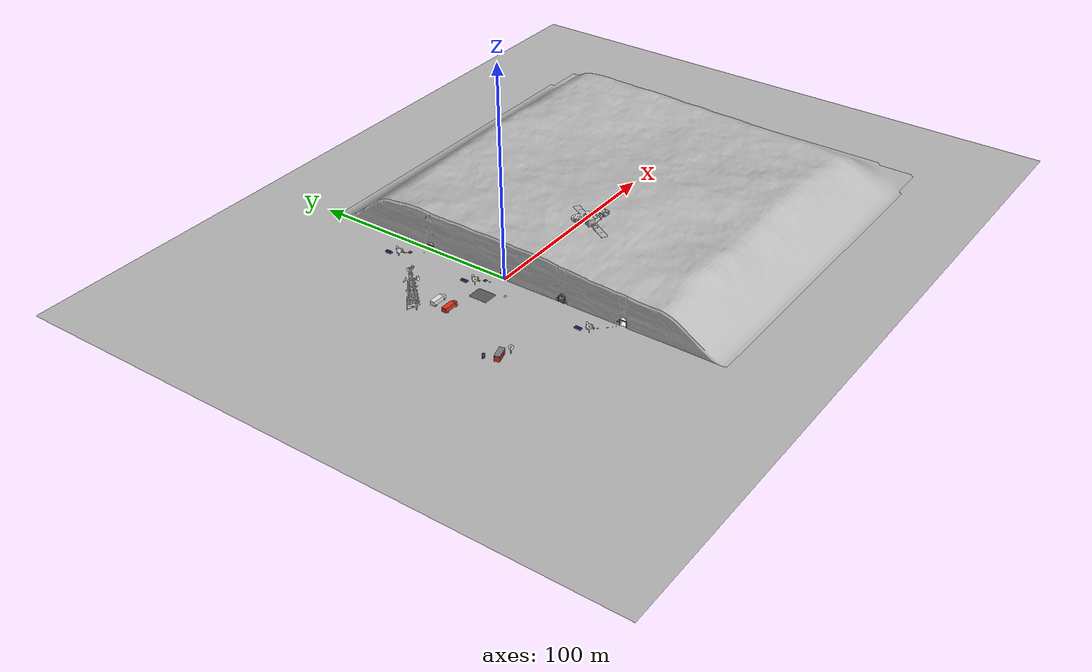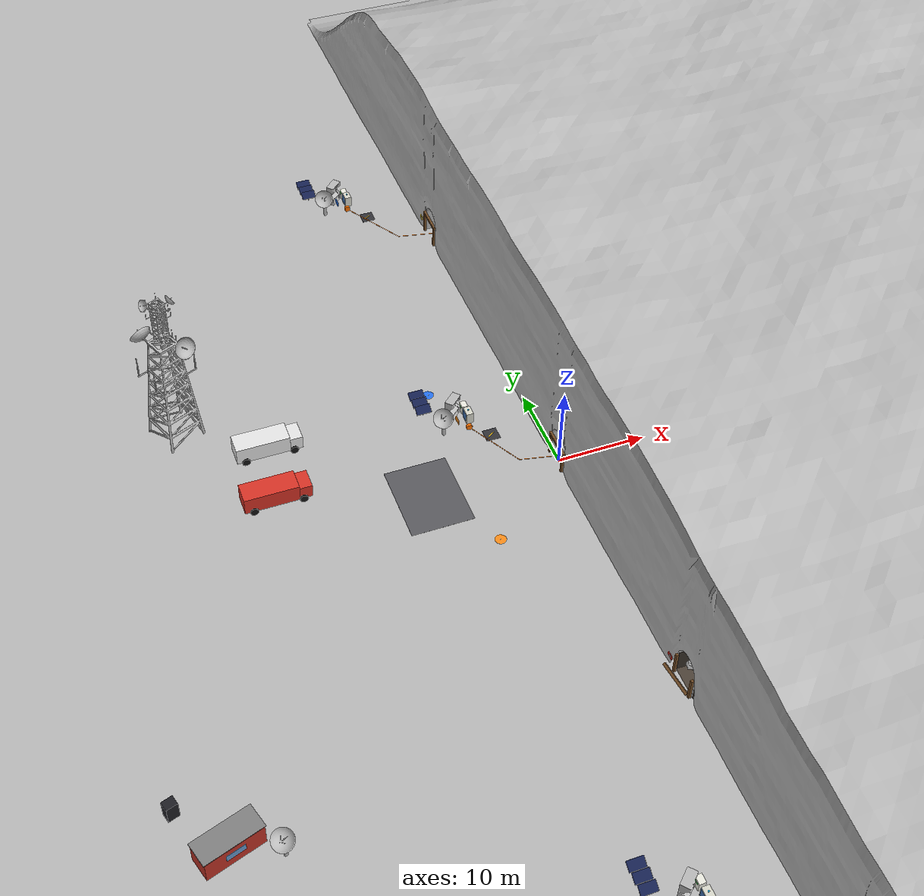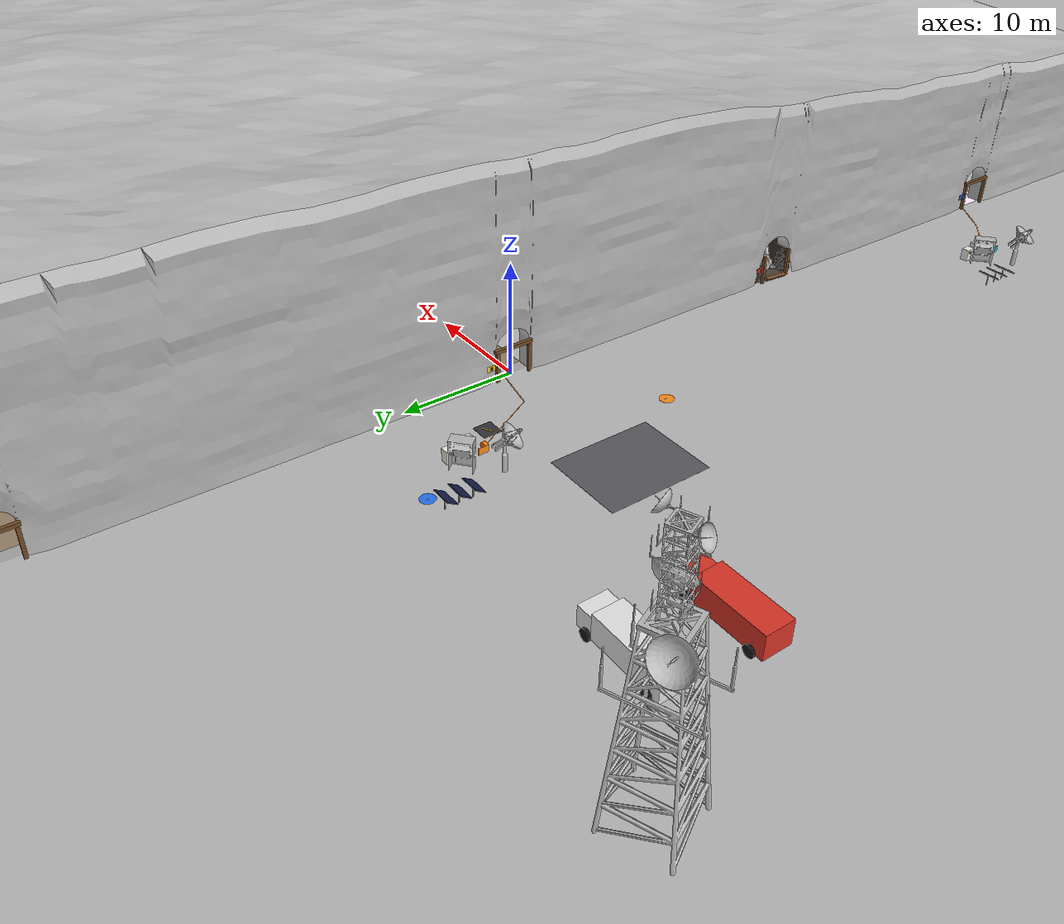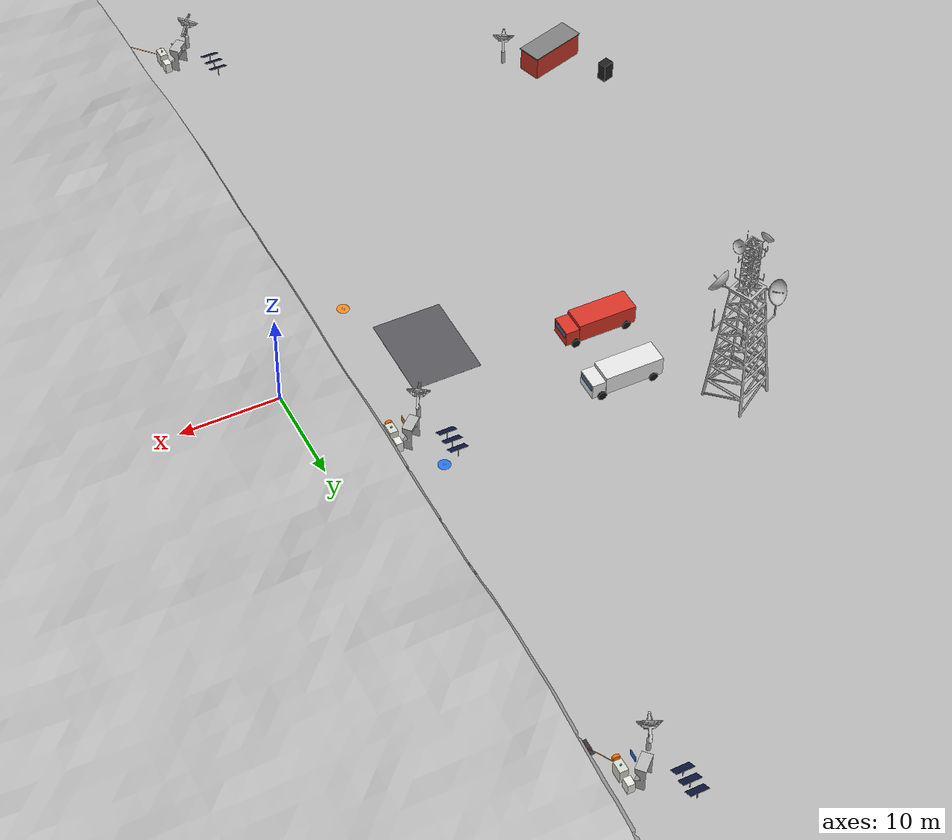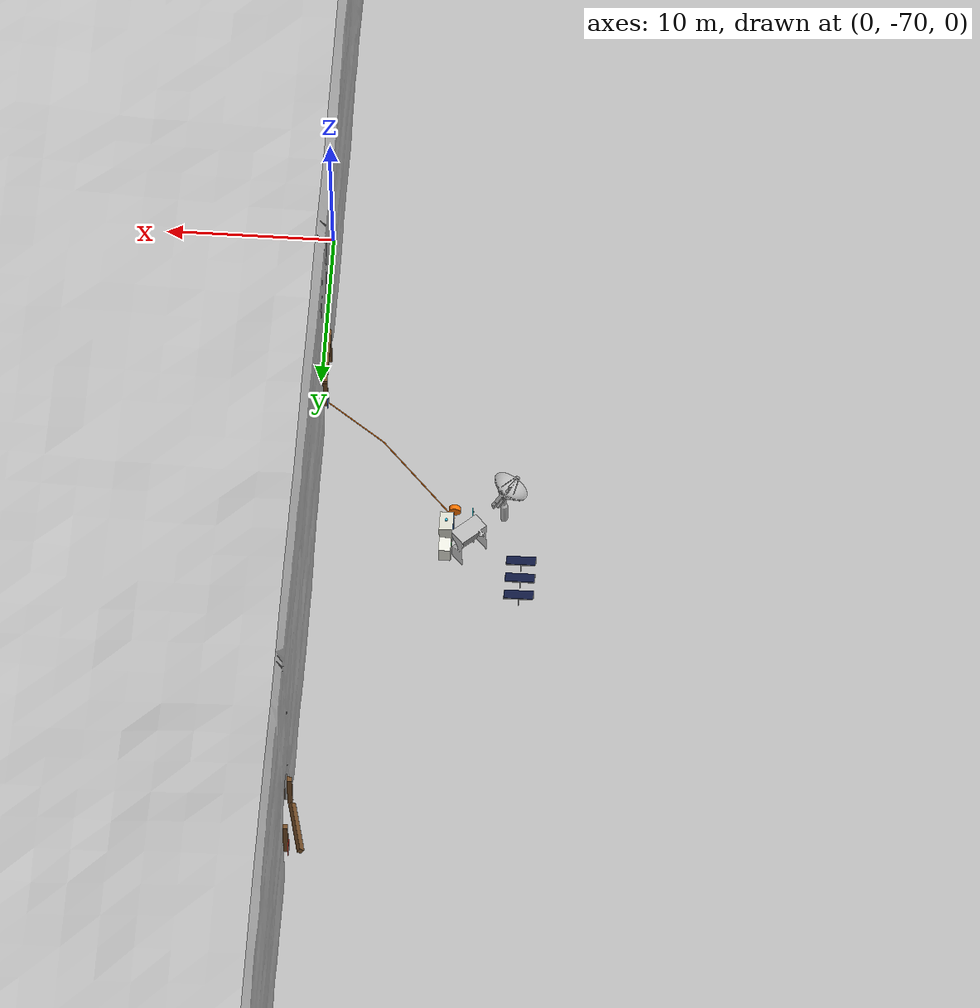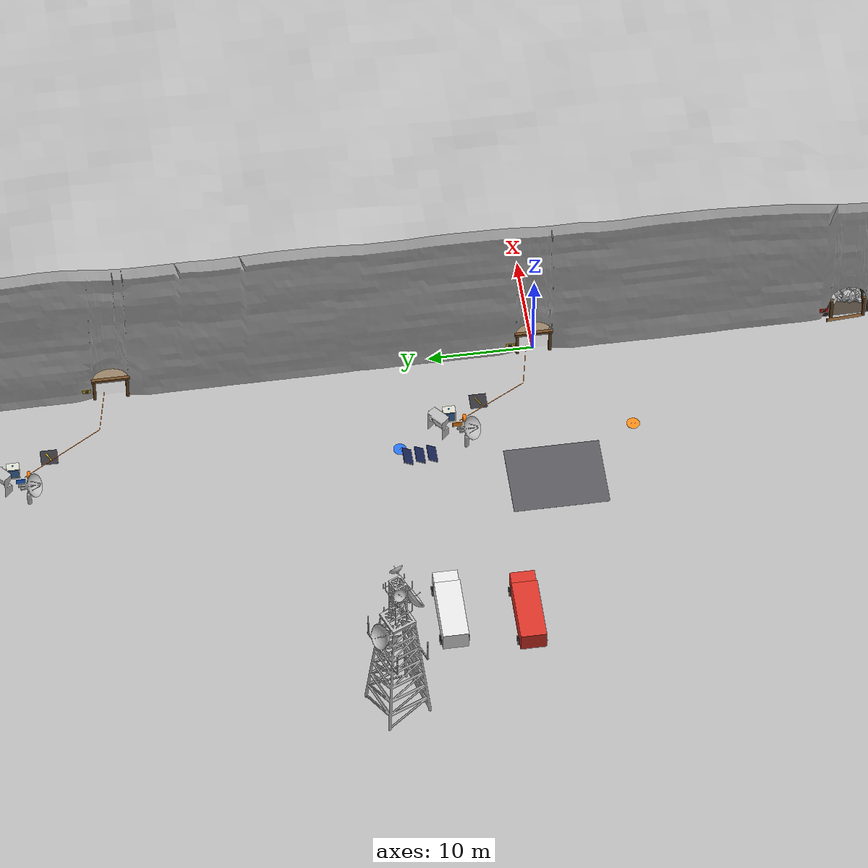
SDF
<sdf version="1.9">
 <world name="living_map">
  <physics name="4ms" type="ignored">
   <max_step_size>0.004</max_step_size>
   <real_time_factor>1.0</real_time_factor>
  </physics>
  <plugin filename="ignition-gazebo-physics-system" name="ignition::gazebo::systems::Physics"/>
  <plugin filename="ignition-gazebo-user-commands-system" name="ignition::gazebo::systems::UserCommands"/>
  <plugin filename="ignition-gazebo-scene-broadcaster-system" name="ignition::gazebo::systems::SceneBroadcaster"/>
  <plugin filename="ignition-gazebo-sensors-system" name="ignition::gazebo::systems::Sensors">
   <render_engine>ogre2</render_engine>
  </plugin>
  <plugin filename="ignition-gazebo-imu-system" name="ignition::gazebo::systems::Imu"/>
  <plugin filename="ignition-gazebo-particle-emitter2-system" name="ignition::gazebo::systems::ParticleEmitter2"/>
  <scene>
   <ambient>0.35 0.35 0.35 1</ambient>
   <background>0.62 0.72 0.82 1</background>
   <shadows>true</shadows>
   <grid>false</grid>
  </scene>
  <light type="directional" name="sun">
   <pose>0 0 60 0 0 0</pose>
   <diffuse>0.95 0.92 0.85 1</diffuse>
   <specular>0.3 0.3 0.3 1</specular>
   <direction>0.45 0.25 -0.85</direction>
   <visualize>false</visualize>
  </light>
  <light type="point" name="lamp0">
   <pose>8 0 3.2 0 0 0</pose>
   <diffuse>1 0.72 0.42 1</diffuse>
   <specular>0.1 0.1 0.1 1</specular>
   <attenuation>
    <range>14</range>
    <constant>0.4</constant>
    <linear>0.05</linear>
    <quadratic>0.008</quadratic>
   </attenuation>
   <cast_shadows>false</cast_shadows>
   <visualize>false</visualize>
  </light>
  <light type="point" name="lamp1">
   <pose>30 0 3.2 0 0 0</pose>
   <diffuse>1 0.72 0.42 1</diffuse>
   <specular>0.1 0.1 0.1 1</specular>
   <attenuation>
    <range>14</range>
    <constant>0.4</constant>
    <linear>0.05</linear>
    <quadratic>0.008</quadratic>
   </attenuation>
   <cast_shadows>false</cast_shadows>
   <visualize>false</visualize>
  </light>
  <light type="point" name="lamp2">
   <pose>58 0 3.2 0 0 0</pose>
   <diffuse>1 0.72 0.42 1</diffuse>
   <specular>0.1 0.1 0.1 1</specular>
   <attenuation>
    <range>14</range>
    <constant>0.4</constant>
    <linear>0.05</linear>
    <quadratic>0.008</quadratic>
   </attenuation>
   <cast_shadows>false</cast_shadows>
   <visualize>false</visualize>
  </light>
  <light type="point" name="lamp3">
   <pose>90 0 3.2 0 0 0</pose>
   <diffuse>1 0.72 0.42 1</diffuse>
   <specular>0.1 0.1 0.1 1</specular>
   <attenuation>
    <range>14</range>
    <constant>0.4</constant>
    <linear>0.05</linear>
    <quadratic>0.008</quadratic>
   </attenuation>
   <cast_shadows>false</cast_shadows>
   <visualize>false</visualize>
  </light>
  <light type="point" name="lamp4">
   <pose>122 0 3.2 0 0 0</pose>
   <diffuse>1 0.72 0.42 1</diffuse>
   <specular>0.1 0.1 0.1 1</specular>
   <attenuation>
    <range>14</range>
    <constant>0.4</constant>
    <linear>0.05</linear>
    <quadratic>0.008</quadratic>
   </attenuation>
   <cast_shadows>false</cast_shadows>
   <visualize>false</visualize>
  </light>
  <light type="point" name="lamp5">
   <pose>50 14 3.2 0 0 0</pose>
   <diffuse>1 0.72 0.42 1</diffuse>
   <specular>0.1 0.1 0.1 1</specular>
   <attenuation>
    <range>14</range>
    <constant>0.4</constant>
    <linear>0.05</linear>
    <quadratic>0.008</quadratic>
   </attenuation>
   <cast_shadows>false</cast_shadows>
   <visualize>false</visualize>
  </light>
  <light type="point" name="lamp6">
   <pose>70 -12 3.2 0 0 0</pose>
   <diffuse>1 0.72 0.42 1</diffuse>
   <specular>0.1 0.1 0.1 1</specular>
   <attenuation>
    <range>14</range>
    <constant>0.4</constant>
    <linear>0.05</linear>
    <quadratic>0.008</quadratic>
   </attenuation>
   <cast_shadows>false</cast_shadows>
   <visualize>false</visualize>
  </light>
  <light type="point" name="lamp7">
   <pose>70 -24 3.2 0 0 0</pose>
   <diffuse>1 0.72 0.42 1</diffuse>
   <specular>0.1 0.1 0.1 1</specular>
   <attenuation>
    <range>14</range>
    <constant>0.4</constant>
    <linear>0.05</linear>
    <quadratic>0.008</quadratic>
   </attenuation>
   <cast_shadows>false</cast_shadows>
   <visualize>false</visualize>
  </light>
  <light type="point" name="lamp8">
   <pose>70 22 3.2 0 0 0</pose>
   <diffuse>1 0.72 0.42 1</diffuse>
   <specular>0.1 0.1 0.1 1</specular>
   <attenuation>
    <range>14</range>
    <constant>0.4</constant>
    <linear>0.05</linear>
    <quadratic>0.008</quadratic>
   </attenuation>
   <cast_shadows>false</cast_shadows>
   <visualize>false</visualize>
  </light>
  <light type="point" name="lamp9">
   <pose>15 40 3.2 0 0 0</pose>
   <diffuse>1 0.72 0.42 1</diffuse>
   <specular>0.1 0.1 0.1 1</specular>
   <attenuation>
    <range>14</range>
    <constant>0.4</constant>
    <linear>0.05</linear>
    <quadratic>0.008</quadratic>
   </attenuation>
   <cast_shadows>false</cast_shadows>
   <visualize>false</visualize>
  </light>
  <light type="point" name="lamp10">
   <pose>45 40 3.2 0 0 0</pose>
   <diffuse>1 0.72 0.42 1</diffuse>
   <specular>0.1 0.1 0.1 1</specular>
   <attenuation>
    <range>14</range>
    <constant>0.4</constant>
    <linear>0.05</linear>
    <quadratic>0.008</quadratic>
   </attenuation>
   <cast_shadows>false</cast_shadows>
   <visualize>false</visualize>
  </light>
  <light type="point" name="lamp11">
   <pose>70 -60 3.2 0 0 0</pose>
   <diffuse>1 0.72 0.42 1</diffuse>
   <specular>0.1 0.1 0.1 1</specular>
   <attenuation>
    <range>14</range>
    <constant>0.4</constant>
    <linear>0.05</linear>
    <quadratic>0.008</quadratic>
   </attenuation>
   <cast_shadows>false</cast_shadows>
   <visualize>false</visualize>
  </light>
  <light type="point" name="lamp12">
   <pose>1.5 -30 3.2 0 0 0</pose>
   <diffuse>1 0.72 0.42 1</diffuse>
   <specular>0.1 0.1 0.1 1</specular>
   <attenuation>
    <range>14</range>
    <constant>0.4</constant>
    <linear>0.05</linear>
    <quadratic>0.008</quadratic>
   </attenuation>
   <cast_shadows>false</cast_shadows>
   <visualize>false</visualize>
  </light>
  <light type="point" name="sump0">
   <pose>20 -60 -3.80 0 0 0</pose>
   <diffuse>0.3 0.7 0.8 1</diffuse>
   <specular>0.1 0.1 0.1 1</specular>
   <attenuation>
    <range>11</range>
    <constant>0.6</constant>
    <linear>0.08</linear>
    <quadratic>0.02</quadratic>
   </attenuation>
   <cast_shadows>false</cast_shadows>
   <visualize>false</visualize>
  </light>
  <light type="point" name="sump1">
   <pose>42 -60 -3.30 0 0 0</pose>
   <diffuse>0.3 0.7 0.8 1</diffuse>
   <specular>0.1 0.1 0.1 1</specular>
   <attenuation>
    <range>11</range>
    <constant>0.6</constant>
    <linear>0.08</linear>
    <quadratic>0.02</quadratic>
   </attenuation>
   <cast_shadows>false</cast_shadows>
   <visualize>false</visualize>
  </light>
  <model name="outside_ground">
   <static>true</static>
   <link name="l">
    <pose>-65 -5 -0.5 0 0 0</pose>
    <collision name="c"><geometry><box><size>130 290 1.0</size></box></geometry></collision>
   </link>
  </model>
  <model name="terrain">
   <static>true</static>
   <link name="l">
    <visual name="v">
     <geometry><mesh><uri>model://lm_terrain/meshes/terrain.obj</uri></mesh></geometry>
     <cast_shadows>false</cast_shadows>
    </visual>
   </link>
  </model>
  <model name="hillside">
   <static>true</static>
   <link name="l">
    <visual name="v"><geometry><mesh><uri>model://lm_hillside/meshes/hillside.obj</uri></mesh></geometry></visual>
   </link>
  </model>
  <model name="gallery_footprint">
   <static>true</static>
   <link name="l">
    <visual name="fp0">
     <pose>10.0 0.0 -0.33 0 0 0</pose>
     <geometry><box><size>20 4.0 0.02</size></box></geometry>
     <visibility_flags>2</visibility_flags>
     <material>
      <ambient>0.58 0.50 0.40 1</ambient>
      <diffuse>0.58 0.50 0.40 1</diffuse>
      <specular>0.1 0.1 0.1 1</specular>
     </material>
     <cast_shadows>false</cast_shadows>
    </visual>
    <visual name="fp1">
     <pose>30.0 0.0 -0.33 0 0 0</pose>
     <geometry><box><size>20 4.0 0.02</size></box></geometry>
     <visibility_flags>2</visibility_flags>
     <material>
      <ambient>0.58 0.50 0.40 1</ambient>
      <diffuse>0.58 0.50 0.40 1</diffuse>
      <specular>0.1 0.1 0.1 1</specular>
     </material>
     <cast_shadows>false</cast_shadows>
    </visual>
    <visual name="fp2">
     <pose>50.0 0.0 -0.33 0 0 0</pose>
     <geometry><box><size>20 4.0 0.02</size></box></geometry>
     <visibility_flags>2</visibility_flags>
     <material>
      <ambient>0.58 0.50 0.40 1</ambient>
      <diffuse>0.58 0.50 0.40 1</diffuse>
      <specular>0.1 0.1 0.1 1</specular>
     </material>
     <cast_shadows>false</cast_shadows>
    </visual>
    <visual name="fp3">
     <pose>50.0 0.0 -0.33 0 0 0</pose>
     <geometry><box><size>4.0 20 0.02</size></box></geometry>
     <visibility_flags>2</visibility_flags>
     <material>
      <ambient>0.58 0.50 0.40 1</ambient>
      <diffuse>0.58 0.50 0.40 1</diffuse>
      <specular>0.1 0.1 0.1 1</specular>
     </material>
     <cast_shadows>false</cast_shadows>
    </visual>
    <visual name="fp4">
     <pose>50.0 20.0 -0.33 0 0 0</pose>
     <geometry><box><size>4.0 20 0.02</size></box></geometry>
     <visibility_flags>2</visibility_flags>
     <material>
      <ambient>0.58 0.50 0.40 1</ambient>
      <diffuse>0.58 0.50 0.40 1</diffuse>
      <specular>0.1 0.1 0.1 1</specular>
     </material>
     <cast_shadows>false</cast_shadows>
    </visual>
    <visual name="fp5">
     <pose>70.0 0.0 -0.33 0 0 0</pose>
     <geometry><box><size>20 4.0 0.02</size></box></geometry>
     <visibility_flags>2</visibility_flags>
     <material>
      <ambient>0.58 0.50 0.40 1</ambient>
      <diffuse>0.58 0.50 0.40 1</diffuse>
      <specular>0.1 0.1 0.1 1</specular>
     </material>
     <cast_shadows>false</cast_shadows>
    </visual>
    <visual name="fp6">
     <pose>70.0 0.0 -0.33 0 0 0</pose>
     <geometry><box><size>4.0 20 0.02</size></box></geometry>
     <visibility_flags>2</visibility_flags>
     <material>
      <ambient>0.58 0.50 0.40 1</ambient>
      <diffuse>0.58 0.50 0.40 1</diffuse>
      <specular>0.1 0.1 0.1 1</specular>
     </material>
     <cast_shadows>false</cast_shadows>
    </visual>
    <visual name="fp7">
     <pose>70.0 -20.0 -0.33 0 0 0</pose>
     <geometry><box><size>4.0 20 0.02</size></box></geometry>
     <visibility_flags>2</visibility_flags>
     <material>
      <ambient>0.58 0.50 0.40 1</ambient>
      <diffuse>0.58 0.50 0.40 1</diffuse>
      <specular>0.1 0.1 0.1 1</specular>
     </material>
     <cast_shadows>false</cast_shadows>
    </visual>
    <visual name="fp8">
     <pose>70.0 20.0 -0.33 0 0 0</pose>
     <geometry><box><size>4.0 20 0.02</size></box></geometry>
     <visibility_flags>2</visibility_flags>
     <material>
      <ambient>0.58 0.50 0.40 1</ambient>
      <diffuse>0.58 0.50 0.40 1</diffuse>
      <specular>0.1 0.1 0.1 1</specular>
     </material>
     <cast_shadows>false</cast_shadows>
    </visual>
    <visual name="fp9">
     <pose>90.0 0.0 -0.33 0 0 0</pose>
     <geometry><box><size>20 4.0 0.02</size></box></geometry>
     <visibility_flags>2</visibility_flags>
     <material>
      <ambient>0.58 0.50 0.40 1</ambient>
      <diffuse>0.58 0.50 0.40 1</diffuse>
      <specular>0.1 0.1 0.1 1</specular>
     </material>
     <cast_shadows>false</cast_shadows>
    </visual>
    <visual name="fp10">
     <pose>110.0 0.0 -0.33 0 0 0</pose>
     <geometry><box><size>20 4.0 0.02</size></box></geometry>
     <visibility_flags>2</visibility_flags>
     <material>
      <ambient>0.58 0.50 0.40 1</ambient>
      <diffuse>0.58 0.50 0.40 1</diffuse>
      <specular>0.1 0.1 0.1 1</specular>
     </material>
     <cast_shadows>false</cast_shadows>
    </visual>
    <visual name="fp11">
     <pose>110.0 0.0 -0.33 0 0 0</pose>
     <geometry><box><size>4.0 20 0.02</size></box></geometry>
     <visibility_flags>2</visibility_flags>
     <material>
      <ambient>0.58 0.50 0.40 1</ambient>
      <diffuse>0.58 0.50 0.40 1</diffuse>
      <specular>0.1 0.1 0.1 1</specular>
     </material>
     <cast_shadows>false</cast_shadows>
    </visual>
    <visual name="fp12">
     <pose>130.0 0.0 -0.33 0 0 0</pose>
     <geometry><box><size>20 4.0 0.02</size></box></geometry>
     <visibility_flags>2</visibility_flags>
     <material>
      <ambient>0.58 0.50 0.40 1</ambient>
      <diffuse>0.58 0.50 0.40 1</diffuse>
      <specular>0.1 0.1 0.1 1</specular>
     </material>
     <cast_shadows>false</cast_shadows>
    </visual>
    <visual name="fp13">
     <pose>10.0 40.0 -0.33 0 0 0</pose>
     <geometry><box><size>20 4.0 0.02</size></box></geometry>
     <visibility_flags>2</visibility_flags>
     <material>
      <ambient>0.58 0.50 0.40 1</ambient>
      <diffuse>0.58 0.50 0.40 1</diffuse>
      <specular>0.1 0.1 0.1 1</specular>
     </material>
     <cast_shadows>false</cast_shadows>
    </visual>
    <visual name="fp14">
     <pose>30.0 40.0 -0.33 0 0 0</pose>
     <geometry><box><size>20 4.0 0.02</size></box></geometry>
     <visibility_flags>2</visibility_flags>
     <material>
      <ambient>0.58 0.50 0.40 1</ambient>
      <diffuse>0.58 0.50 0.40 1</diffuse>
      <specular>0.1 0.1 0.1 1</specular>
     </material>
     <cast_shadows>false</cast_shadows>
    </visual>
    <visual name="fp15">
     <pose>50.0 40.0 -0.33 0 0 0</pose>
     <geometry><box><size>20 4.0 0.02</size></box></geometry>
     <visibility_flags>2</visibility_flags>
     <material>
      <ambient>0.58 0.50 0.40 1</ambient>
      <diffuse>0.58 0.50 0.40 1</diffuse>
      <specular>0.1 0.1 0.1 1</specular>
     </material>
     <cast_shadows>false</cast_shadows>
    </visual>
    <visual name="fp16">
     <pose>70.0 40.0 -0.33 0 0 0</pose>
     <geometry><box><size>20 4.0 0.02</size></box></geometry>
     <visibility_flags>2</visibility_flags>
     <material>
      <ambient>0.58 0.50 0.40 1</ambient>
      <diffuse>0.58 0.50 0.40 1</diffuse>
      <specular>0.1 0.1 0.1 1</specular>
     </material>
     <cast_shadows>false</cast_shadows>
    </visual>
    <visual name="fp17">
     <pose>70.0 40.0 -0.33 0 0 0</pose>
     <geometry><box><size>4.0 20 0.02</size></box></geometry>
     <visibility_flags>2</visibility_flags>
     <material>
      <ambient>0.58 0.50 0.40 1</ambient>
      <diffuse>0.58 0.50 0.40 1</diffuse>
      <specular>0.1 0.1 0.1 1</specular>
     </material>
     <cast_shadows>false</cast_shadows>
    </visual>
    <visual name="fp22">
     <pose>1.25 -30.0 -0.33 0 0 0</pose>
     <geometry><box><size>2.5 3.3999999999999986 0.02</size></box></geometry>
     <visibility_flags>2</visibility_flags>
     <material>
      <ambient>0.58 0.50 0.40 1</ambient>
      <diffuse>0.58 0.50 0.40 1</diffuse>
      <specular>0.1 0.1 0.1 1</specular>
     </material>
     <cast_shadows>false</cast_shadows>
    </visual>
   </link>
  </model>
  <model name="blocker_0">
   <static>true</static>
   <pose>50 -11 4.0 0 0 0</pose>
   <link name="l">
    <collision name="c"><geometry><box><size>12 2.0 12</size></box></geometry></collision>
    <visual name="v">
     <geometry><box><size>12 2.0 12</size></box></geometry>
     <material>
      <ambient>0.22 0.19 0.16 1</ambient>
      <diffuse>0.22 0.19 0.16 1</diffuse>
      <specular>0.05 0.05 0.05 1</specular>
      <pbr>
       <metal>
        <albedo_map>model://lm_rock/materials/textures/rock.png</albedo_map>
        <roughness>0.95</roughness>
        <metalness>0.0</metalness>
       </metal>
      </pbr>
     </material>
    </visual>
   </link>
  </model>
  <model name="blocker_1">
   <static>true</static>
   <pose>50 31 4.0 0 0 0</pose>
   <link name="l">
    <collision name="c"><geometry><box><size>12 2.0 12</size></box></geometry></collision>
    <visual name="v">
     <geometry><box><size>12 2.0 12</size></box></geometry>
     <material>
      <ambient>0.22 0.19 0.16 1</ambient>
      <diffuse>0.22 0.19 0.16 1</diffuse>
      <specular>0.05 0.05 0.05 1</specular>
      <pbr>
       <metal>
        <albedo_map>model://lm_rock/materials/textures/rock.png</albedo_map>
        <roughness>0.95</roughness>
        <metalness>0.0</metalness>
       </metal>
      </pbr>
     </material>
    </visual>
   </link>
  </model>
  <model name="blocker_2">
   <static>true</static>
   <pose>70 -31 4.0 0 0 0</pose>
   <link name="l">
    <collision name="c"><geometry><box><size>12 2.0 12</size></box></geometry></collision>
    <visual name="v">
     <geometry><box><size>12 2.0 12</size></box></geometry>
     <material>
      <ambient>0.22 0.19 0.16 1</ambient>
      <diffuse>0.22 0.19 0.16 1</diffuse>
      <specular>0.05 0.05 0.05 1</specular>
      <pbr>
       <metal>
        <albedo_map>model://lm_rock/materials/textures/rock.png</albedo_map>
        <roughness>0.95</roughness>
        <metalness>0.0</metalness>
       </metal>
      </pbr>
     </material>
    </visual>
   </link>
  </model>
  <model name="blocker_3">
   <static>true</static>
   <pose>110 11 4.0 0 0 0</pose>
   <link name="l">
    <collision name="c"><geometry><box><size>12 2.0 12</size></box></geometry></collision>
    <visual name="v">
     <geometry><box><size>12 2.0 12</size></box></geometry>
     <material>
      <ambient>0.22 0.19 0.16 1</ambient>
      <diffuse>0.22 0.19 0.16 1</diffuse>
      <specular>0.05 0.05 0.05 1</specular>
      <pbr>
       <metal>
        <albedo_map>model://lm_rock/materials/textures/rock.png</albedo_map>
        <roughness>0.95</roughness>
        <metalness>0.0</metalness>
       </metal>
      </pbr>
     </material>
    </visual>
   </link>
  </model>
  <model name="blocker_4">
   <static>true</static>
   <pose>110 -11 4.0 0 0 0</pose>
   <link name="l">
    <collision name="c"><geometry><box><size>12 2.0 12</size></box></geometry></collision>
    <visual name="v">
     <geometry><box><size>12 2.0 12</size></box></geometry>
     <material>
      <ambient>0.22 0.19 0.16 1</ambient>
      <diffuse>0.22 0.19 0.16 1</diffuse>
      <specular>0.05 0.05 0.05 1</specular>
      <pbr>
       <metal>
        <albedo_map>model://lm_rock/materials/textures/rock.png</albedo_map>
        <roughness>0.95</roughness>
        <metalness>0.0</metalness>
       </metal>
      </pbr>
     </material>
    </visual>
   </link>
  </model>
  <model name="blocker_5">
   <static>true</static>
   <pose>141 0 4.0 0 0 0</pose>
   <link name="l">
    <collision name="c"><geometry><box><size>2.0 12 12</size></box></geometry></collision>
    <visual name="v">
     <geometry><box><size>2.0 12 12</size></box></geometry>
     <material>
      <ambient>0.22 0.19 0.16 1</ambient>
      <diffuse>0.22 0.19 0.16 1</diffuse>
      <specular>0.05 0.05 0.05 1</specular>
      <pbr>
       <metal>
        <albedo_map>model://lm_rock/materials/textures/rock.png</albedo_map>
        <roughness>0.95</roughness>
        <metalness>0.0</metalness>
       </metal>
      </pbr>
     </material>
    </visual>
   </link>
  </model>
  <model name="blocker_6">
   <static>true</static>
   <pose>70 51 4.0 0 0 0</pose>
   <link name="l">
    <collision name="c"><geometry><box><size>12 2.0 12</size></box></geometry></collision>
    <visual name="v">
     <geometry><box><size>12 2.0 12</size></box></geometry>
     <material>
      <ambient>0.22 0.19 0.16 1</ambient>
      <diffuse>0.22 0.19 0.16 1</diffuse>
      <specular>0.05 0.05 0.05 1</specular>
      <pbr>
       <metal>
        <albedo_map>model://lm_rock/materials/textures/rock.png</albedo_map>
        <roughness>0.95</roughness>
        <metalness>0.0</metalness>
       </metal>
      </pbr>
     </material>
    </visual>
   </link>
  </model>
  <model name="blocker_7">
   <static>true</static>
   <pose>81 40 4.0 0 0 0</pose>
   <link name="l">
    <collision name="c"><geometry><box><size>2.0 12 12</size></box></geometry></collision>
    <visual name="v">
     <geometry><box><size>2.0 12 12</size></box></geometry>
     <material>
      <ambient>0.22 0.19 0.16 1</ambient>
      <diffuse>0.22 0.19 0.16 1</diffuse>
      <specular>0.05 0.05 0.05 1</specular>
      <pbr>
       <metal>
        <albedo_map>model://lm_rock/materials/textures/rock.png</albedo_map>
        <roughness>0.95</roughness>
        <metalness>0.0</metalness>
       </metal>
      </pbr>
     </material>
    </visual>
   </link>
  </model>
  <model name="blocker_8">
   <static>true</static>
   <pose>81 -60 4.0 0 0 0</pose>
   <link name="l">
    <collision name="c"><geometry><box><size>2.0 12 12</size></box></geometry></collision>
    <visual name="v">
     <geometry><box><size>2.0 12 12</size></box></geometry>
     <material>
      <ambient>0.22 0.19 0.16 1</ambient>
      <diffuse>0.22 0.19 0.16 1</diffuse>
      <specular>0.05 0.05 0.05 1</specular>
      <pbr>
       <metal>
        <albedo_map>model://lm_rock/materials/textures/rock.png</albedo_map>
        <roughness>0.95</roughness>
        <metalness>0.0</metalness>
       </metal>
      </pbr>
     </material>
    </visual>
   </link>
  </model>
  <model name="portal_sets">
   <static>true</static>
   <link name="post_Aa">
    <pose>-0.4 38.45 1.35 0 0 0</pose>
    <visual name="v">
     <geometry><box><size>0.28 0.28 2.7</size></box></geometry>
     <material>
      <ambient>0.45 0.30 0.15 1</ambient>
      <diffuse>0.45 0.30 0.15 1</diffuse>
      <specular>0.1 0.1 0.1 1</specular>
     </material>
     <cast_shadows>false</cast_shadows>
    </visual>
   </link>
   <link name="post_Ab">
    <pose>-0.4 41.55 1.35 0 0 0</pose>
    <visual name="v">
     <geometry><box><size>0.28 0.28 2.7</size></box></geometry>
     <material>
      <ambient>0.45 0.30 0.15 1</ambient>
      <diffuse>0.45 0.30 0.15 1</diffuse>
      <specular>0.1 0.1 0.1 1</specular>
     </material>
     <cast_shadows>false</cast_shadows>
    </visual>
   </link>
   <link name="cap_A">
    <pose>-0.4 40.0 2.8 0 0 0</pose>
    <visual name="v">
     <geometry><box><size>0.3 3.6 0.3</size></box></geometry>
     <material>
      <ambient>0.45 0.30 0.15 1</ambient>
      <diffuse>0.45 0.30 0.15 1</diffuse>
      <specular>0.1 0.1 0.1 1</specular>
     </material>
     <cast_shadows>false</cast_shadows>
    </visual>
   </link>
   <link name="sign_A">
    <pose>-0.62 42.3 1.6 0 0 0</pose>
    <visual name="v">
     <geometry><box><size>0.04 0.8 0.5</size></box></geometry>
     <material>
      <ambient>0.95 0.8 0.1 1</ambient>
      <diffuse>0.95 0.8 0.1 1</diffuse>
      <specular>0.1 0.1 0.1 1</specular>
     </material>
     <cast_shadows>false</cast_shadows>
    </visual>
   </link>
   <link name="label_A">
    <pose>-0.65 42.3 1.6 0 0 0</pose>
    <visual name="v">
     <geometry><box><size>0.02 0.3 0.3</size></box></geometry>
     <material>
      <ambient>0.1 0.1 0.1 1</ambient>
      <diffuse>0.1 0.1 0.1 1</diffuse>
      <specular>0.1 0.1 0.1 1</specular>
     </material>
     <cast_shadows>false</cast_shadows>
    </visual>
   </link>
   <link name="post_Ba">
    <pose>-0.4 -1.55 1.35 0 0 0</pose>
    <visual name="v">
     <geometry><box><size>0.28 0.28 2.7</size></box></geometry>
     <material>
      <ambient>0.45 0.30 0.15 1</ambient>
      <diffuse>0.45 0.30 0.15 1</diffuse>
      <specular>0.1 0.1 0.1 1</specular>
     </material>
     <cast_shadows>false</cast_shadows>
    </visual>
   </link>
   <link name="post_Bb">
    <pose>-0.4 1.55 1.35 0 0 0</pose>
    <visual name="v">
     <geometry><box><size>0.28 0.28 2.7</size></box></geometry>
     <material>
      <ambient>0.45 0.30 0.15 1</ambient>
      <diffuse>0.45 0.30 0.15 1</diffuse>
      <specular>0.1 0.1 0.1 1</specular>
     </material>
     <cast_shadows>false</cast_shadows>
    </visual>
   </link>
   <link name="cap_B">
    <pose>-0.4 0.0 2.8 0 0 0</pose>
    <visual name="v">
     <geometry><box><size>0.3 3.6 0.3</size></box></geometry>
     <material>
      <ambient>0.45 0.30 0.15 1</ambient>
      <diffuse>0.45 0.30 0.15 1</diffuse>
      <specular>0.1 0.1 0.1 1</specular>
     </material>
     <cast_shadows>false</cast_shadows>
    </visual>
   </link>
   <link name="sign_B">
    <pose>-0.62 2.3 1.6 0 0 0</pose>
    <visual name="v">
     <geometry><box><size>0.04 0.8 0.5</size></box></geometry>
     <material>
      <ambient>0.95 0.8 0.1 1</ambient>
      <diffuse>0.95 0.8 0.1 1</diffuse>
      <specular>0.1 0.1 0.1 1</specular>
     </material>
     <cast_shadows>false</cast_shadows>
    </visual>
   </link>
   <link name="label_B">
    <pose>-0.65 2.3 1.6 0 0 0</pose>
    <visual name="v">
     <geometry><box><size>0.02 0.3 0.3</size></box></geometry>
     <material>
      <ambient>0.1 0.1 0.1 1</ambient>
      <diffuse>0.1 0.1 0.1 1</diffuse>
      <specular>0.1 0.1 0.1 1</specular>
     </material>
     <cast_shadows>false</cast_shadows>
    </visual>
   </link>
   <link name="post_Ca">
    <pose>-0.4 -61.55 1.35 0 0 0</pose>
    <visual name="v">
     <geometry><box><size>0.28 0.28 2.7</size></box></geometry>
     <material>
      <ambient>0.45 0.30 0.15 1</ambient>
      <diffuse>0.45 0.30 0.15 1</diffuse>
      <specular>0.1 0.1 0.1 1</specular>
     </material>
     <cast_shadows>false</cast_shadows>
    </visual>
   </link>
   <link name="post_Cb">
    <pose>-0.4 -58.45 1.35 0 0 0</pose>
    <visual name="v">
     <geometry><box><size>0.28 0.28 2.7</size></box></geometry>
     <material>
      <ambient>0.45 0.30 0.15 1</ambient>
      <diffuse>0.45 0.30 0.15 1</diffuse>
      <specular>0.1 0.1 0.1 1</specular>
     </material>
     <cast_shadows>false</cast_shadows>
    </visual>
   </link>
   <link name="cap_C">
    <pose>-0.4 -60.0 2.8 0 0 0</pose>
    <visual name="v">
     <geometry><box><size>0.3 3.6 0.3</size></box></geometry>
     <material>
      <ambient>0.45 0.30 0.15 1</ambient>
      <diffuse>0.45 0.30 0.15 1</diffuse>
      <specular>0.1 0.1 0.1 1</specular>
     </material>
     <cast_shadows>false</cast_shadows>
    </visual>
   </link>
   <link name="sign_C">
    <pose>-0.62 -57.7 1.6 0 0 0</pose>
    <visual name="v">
     <geometry><box><size>0.04 0.8 0.5</size></box></geometry>
     <material>
      <ambient>0.1 0.35 0.9 1</ambient>
      <diffuse>0.1 0.35 0.9 1</diffuse>
      <specular>0.1 0.1 0.1 1</specular>
     </material>
     <cast_shadows>false</cast_shadows>
    </visual>
   </link>
   <link name="label_C">
    <pose>-0.65 -57.7 1.6 0 0 0</pose>
    <visual name="v">
     <geometry><box><size>0.02 0.3 0.3</size></box></geometry>
     <material>
      <ambient>0.1 0.1 0.1 1</ambient>
      <diffuse>0.1 0.1 0.1 1</diffuse>
      <specular>0.1 0.1 0.1 1</specular>
     </material>
     <cast_shadows>false</cast_shadows>
    </visual>
   </link>
   <link name="post_Da">
    <pose>-0.4 -31.55 1.35 0 0 0</pose>
    <visual name="v">
     <geometry><box><size>0.28 0.28 2.7</size></box></geometry>
     <material>
      <ambient>0.45 0.30 0.15 1</ambient>
      <diffuse>0.45 0.30 0.15 1</diffuse>
      <specular>0.1 0.1 0.1 1</specular>
     </material>
     <cast_shadows>false</cast_shadows>
    </visual>
   </link>
   <link name="post_Db">
    <pose>-0.4 -28.45 1.35 0 0 0</pose>
    <visual name="v">
     <geometry><box><size>0.28 0.28 2.7</size></box></geometry>
     <material>
      <ambient>0.45 0.30 0.15 1</ambient>
      <diffuse>0.45 0.30 0.15 1</diffuse>
      <specular>0.1 0.1 0.1 1</specular>
     </material>
     <cast_shadows>false</cast_shadows>
    </visual>
   </link>
   <link name="cap_D">
    <pose>-0.9 -29.6 0.55 0.35 0.9 0.5</pose>
    <visual name="v">
     <geometry><box><size>0.3 3.6 0.3</size></box></geometry>
     <material>
      <ambient>0.45 0.30 0.15 1</ambient>
      <diffuse>0.45 0.30 0.15 1</diffuse>
      <specular>0.1 0.1 0.1 1</specular>
     </material>
     <cast_shadows>false</cast_shadows>
    </visual>
   </link>
   <link name="sign_D">
    <pose>-0.62 -27.7 1.6 0 0 0</pose>
    <visual name="v">
     <geometry><box><size>0.04 0.8 0.5</size></box></geometry>
     <material>
      <ambient>0.85 0.15 0.1 1</ambient>
      <diffuse>0.85 0.15 0.1 1</diffuse>
      <specular>0.1 0.1 0.1 1</specular>
     </material>
     <cast_shadows>false</cast_shadows>
    </visual>
   </link>
   <link name="label_D">
    <pose>-0.65 -27.7 1.6 0 0 0</pose>
    <visual name="v">
     <geometry><box><size>0.02 0.3 0.3</size></box></geometry>
     <material>
      <ambient>0.1 0.1 0.1 1</ambient>
      <diffuse>0.1 0.1 0.1 1</diffuse>
      <specular>0.1 0.1 0.1 1</specular>
     </material>
     <cast_shadows>false</cast_shadows>
    </visual>
   </link>
  </model>
  <model name="adit_d">
   <static>true</static>
   <link name="adit_wall-1">
    <pose>2.25 -32.0 2.4 0 0 0</pose>
    <collision name="c"><geometry><box><size>4.7 0.6 5.2</size></box></geometry></collision>
    <visual name="v">
     <geometry><box><size>4.7 0.6 5.2</size></box></geometry>
     <material>
      <ambient>0.22 0.19 0.16 1</ambient>
      <diffuse>0.22 0.19 0.16 1</diffuse>
      <specular>0.1 0.1 0.1 1</specular>
     </material>
     <cast_shadows>false</cast_shadows>
    </visual>
   </link>
   <link name="adit_wall1">
    <pose>2.25 -28.0 2.4 0 0 0</pose>
    <collision name="c"><geometry><box><size>4.7 0.6 5.2</size></box></geometry></collision>
    <visual name="v">
     <geometry><box><size>4.7 0.6 5.2</size></box></geometry>
     <material>
      <ambient>0.22 0.19 0.16 1</ambient>
      <diffuse>0.22 0.19 0.16 1</diffuse>
      <specular>0.1 0.1 0.1 1</specular>
     </material>
     <cast_shadows>false</cast_shadows>
    </visual>
   </link>
   <link name="adit_roof">
    <pose>2.25 -30.0 4.95 0 0 0</pose>
    <visual name="v">
     <geometry><box><size>4.7 4.6 0.3</size></box></geometry>
     <material>
      <ambient>0.22 0.19 0.16 1</ambient>
      <diffuse>0.22 0.19 0.16 1</diffuse>
      <specular>0.1 0.1 0.1 1</specular>
     </material>
     <cast_shadows>false</cast_shadows>
    </visual>
   </link>
   <link name="adit_floor">
    <pose>2.25 -30.0 -0.1 0 0 0</pose>
    <collision name="c"><geometry><box><size>4.7 4.6 0.2</size></box></geometry></collision>
    <visual name="v">
     <geometry><box><size>4.7 4.6 0.2</size></box></geometry>
     <material>
      <ambient>0.30 0.26 0.22 1</ambient>
      <diffuse>0.30 0.26 0.22 1</diffuse>
      <specular>0.1 0.1 0.1 1</specular>
     </material>
     <cast_shadows>false</cast_shadows>
    </visual>
   </link>
   <link name="adit_plug">
    <pose>3.7 -30.0 2.4 0 0 0</pose>
    <collision name="c"><geometry><box><size>2.2 4.0 5.0</size></box></geometry></collision>
    <visual name="v">
     <geometry><box><size>2.2 4.0 5.0</size></box></geometry>
     <material>
      <ambient>0.22 0.19 0.16 1</ambient>
      <diffuse>0.22 0.19 0.16 1</diffuse>
      <specular>0.1 0.1 0.1 1</specular>
     </material>
     <cast_shadows>false</cast_shadows>
    </visual>
   </link>
   <link name="rubble">
    <visual name="r0">
     <pose>2.22 -28.83 1.41 0.02 1.51 2.69</pose>
     <geometry><mesh><uri>model://lm_rock/meshes/rock.obj</uri><scale>2.45 2.45 2.45</scale></mesh></geometry>
    </visual>
    <visual name="r1">
     <pose>2.65 -31.47 2.04 1.14 2.11 1.36</pose>
     <geometry><mesh><uri>model://lm_rock/meshes/rock.obj</uri><scale>1.91 1.91 1.91</scale></mesh></geometry>
    </visual>
    <visual name="r2">
     <pose>2.31 -31.24 0.65 1.52 2.77 1.77</pose>
     <geometry><mesh><uri>model://lm_rock/meshes/rock.obj</uri><scale>2.82 2.82 2.82</scale></mesh></geometry>
    </visual>
    <visual name="r3">
     <pose>2.77 -31.27 1.44 0.87 2.02 2.18</pose>
     <geometry><mesh><uri>model://lm_rock/meshes/rock.obj</uri><scale>2.88 2.88 2.88</scale></mesh></geometry>
    </visual>
    <visual name="r4">
     <pose>2.34 -30.93 0.41 0.84 2.43 0.60</pose>
     <geometry><mesh><uri>model://lm_rock/meshes/rock.obj</uri><scale>2.39 2.39 2.39</scale></mesh></geometry>
    </visual>
    <visual name="r5">
     <pose>2.15 -30.39 3.18 1.48 0.07 1.27</pose>
     <geometry><mesh><uri>model://lm_rock/meshes/rock.obj</uri><scale>3.04 3.04 3.04</scale></mesh></geometry>
    </visual>
    <visual name="r6">
     <pose>2.64 -31.21 0.49 1.74 2.69 0.61</pose>
     <geometry><mesh><uri>model://lm_rock/meshes/rock.obj</uri><scale>3.07 3.07 3.07</scale></mesh></geometry>
    </visual>
    <visual name="r7">
     <pose>2.59 -31.54 0.39 0.25 1.49 2.76</pose>
     <geometry><mesh><uri>model://lm_rock/meshes/rock.obj</uri><scale>1.81 1.81 1.81</scale></mesh></geometry>
    </visual>
    <visual name="r8">
     <pose>2.67 -31.30 1.49 1.74 0.52 1.83</pose>
     <geometry><mesh><uri>model://lm_rock/meshes/rock.obj</uri><scale>2.39 2.39 2.39</scale></mesh></geometry>
    </visual>
    <visual name="r9">
     <pose>2.60 -29.66 0.29 0.45 0.80 2.98</pose>
     <geometry><mesh><uri>model://lm_rock/meshes/rock.obj</uri><scale>3.14 3.14 3.14</scale></mesh></geometry>
    </visual>
    <visual name="r10">
     <pose>2.73 -28.56 0.52 0.71 1.83 0.13</pose>
     <geometry><mesh><uri>model://lm_rock/meshes/rock.obj</uri><scale>3.20 3.20 3.20</scale></mesh></geometry>
    </visual>
    <visual name="r11">
     <pose>2.63 -29.12 2.46 0.26 1.04 2.59</pose>
     <geometry><mesh><uri>model://lm_rock/meshes/rock.obj</uri><scale>2.31 2.31 2.31</scale></mesh></geometry>
    </visual>
    <visual name="r12">
     <pose>2.46 -28.44 1.68 1.72 0.06 2.40</pose>
     <geometry><mesh><uri>model://lm_rock/meshes/rock.obj</uri><scale>2.62 2.62 2.62</scale></mesh></geometry>
    </visual>
    <visual name="r13">
     <pose>2.29 -30.18 1.62 0.97 0.27 1.89</pose>
     <geometry><mesh><uri>model://lm_rock/meshes/rock.obj</uri><scale>2.26 2.26 2.26</scale></mesh></geometry>
    </visual>
    <visual name="r14">
     <pose>2.12 -29.10 2.84 2.42 1.49 2.13</pose>
     <geometry><mesh><uri>model://lm_rock/meshes/rock.obj</uri><scale>1.94 1.94 1.94</scale></mesh></geometry>
    </visual>
    <visual name="r15">
     <pose>2.48 -30.86 2.68 2.89 1.20 1.12</pose>
     <geometry><mesh><uri>model://lm_rock/meshes/rock.obj</uri><scale>2.15 2.15 2.15</scale></mesh></geometry>
    </visual>
    <visual name="r16">
     <pose>2.70 -31.05 1.39 2.53 0.78 0.15</pose>
     <geometry><mesh><uri>model://lm_rock/meshes/rock.obj</uri><scale>3.00 3.00 3.00</scale></mesh></geometry>
    </visual>
    <visual name="r17">
     <pose>2.95 -28.44 0.70 1.82 0.04 0.18</pose>
     <geometry><mesh><uri>model://lm_rock/meshes/rock.obj</uri><scale>3.17 3.17 3.17</scale></mesh></geometry>
    </visual>
    <visual name="r18">
     <pose>2.65 -28.51 1.46 1.06 0.42 1.69</pose>
     <geometry><mesh><uri>model://lm_rock/meshes/rock.obj</uri><scale>2.09 2.09 2.09</scale></mesh></geometry>
    </visual>
    <visual name="r19">
     <pose>2.60 -29.37 0.40 0.20 1.35 2.11</pose>
     <geometry><mesh><uri>model://lm_rock/meshes/rock.obj</uri><scale>1.99 1.99 1.99</scale></mesh></geometry>
    </visual>
    <visual name="r20">
     <pose>2.90 -31.06 1.44 2.15 2.32 2.64</pose>
     <geometry><mesh><uri>model://lm_rock/meshes/rock.obj</uri><scale>2.87 2.87 2.87</scale></mesh></geometry>
    </visual>
    <visual name="r21">
     <pose>2.14 -29.91 0.45 0.52 1.89 0.25</pose>
     <geometry><mesh><uri>model://lm_rock/meshes/rock.obj</uri><scale>2.49 2.49 2.49</scale></mesh></geometry>
    </visual>
    <visual name="r22">
     <pose>2.11 -31.04 0.88 1.37 1.68 1.16</pose>
     <geometry><mesh><uri>model://lm_rock/meshes/rock.obj</uri><scale>2.89 2.89 2.89</scale></mesh></geometry>
    </visual>
    <visual name="r23">
     <pose>2.95 -29.89 1.79 2.82 0.09 2.98</pose>
     <geometry><mesh><uri>model://lm_rock/meshes/rock.obj</uri><scale>2.04 2.04 2.04</scale></mesh></geometry>
    </visual>
    <visual name="r24">
     <pose>2.57 -29.88 2.01 2.73 0.20 1.93</pose>
     <geometry><mesh><uri>model://lm_rock/meshes/rock.obj</uri><scale>3.04 3.04 3.04</scale></mesh></geometry>
    </visual>
    <visual name="r25">
     <pose>2.75 -29.29 1.15 0.31 2.10 1.36</pose>
     <geometry><mesh><uri>model://lm_rock/meshes/rock.obj</uri><scale>2.56 2.56 2.56</scale></mesh></geometry>
    </visual>
    <visual name="r26">
     <pose>2.15 -29.67 2.33 1.12 2.64 0.69</pose>
     <geometry><mesh><uri>model://lm_rock/meshes/rock.obj</uri><scale>2.49 2.49 2.49</scale></mesh></geometry>
    </visual>
    <visual name="r27">
     <pose>2.66 -28.80 2.65 0.11 1.79 1.84</pose>
     <geometry><mesh><uri>model://lm_rock/meshes/rock.obj</uri><scale>2.95 2.95 2.95</scale></mesh></geometry>
    </visual>
    <visual name="r28">
     <pose>2.16 -30.99 1.52 1.82 0.54 0.19</pose>
     <geometry><mesh><uri>model://lm_rock/meshes/rock.obj</uri><scale>2.75 2.75 2.75</scale></mesh></geometry>
    </visual>
    <visual name="r29">
     <pose>2.58 -31.52 1.75 2.33 1.00 2.35</pose>
     <geometry><mesh><uri>model://lm_rock/meshes/rock.obj</uri><scale>2.30 2.30 2.30</scale></mesh></geometry>
    </visual>
    <visual name="r30">
     <pose>2.63 -28.48 3.44 2.96 2.50 0.32</pose>
     <geometry><mesh><uri>model://lm_rock/meshes/rock.obj</uri><scale>1.81 1.81 1.81</scale></mesh></geometry>
    </visual>
    <visual name="r31">
     <pose>2.80 -30.99 0.91 0.66 0.33 0.36</pose>
     <geometry><mesh><uri>model://lm_rock/meshes/rock.obj</uri><scale>2.29 2.29 2.29</scale></mesh></geometry>
    </visual>
    <visual name="r32">
     <pose>2.44 -29.23 3.52 1.40 1.57 1.11</pose>
     <geometry><mesh><uri>model://lm_rock/meshes/rock.obj</uri><scale>3.11 3.11 3.11</scale></mesh></geometry>
    </visual>
    <visual name="r33">
     <pose>2.33 -29.94 0.93 0.59 1.32 2.83</pose>
     <geometry><mesh><uri>model://lm_rock/meshes/rock.obj</uri><scale>2.69 2.69 2.69</scale></mesh></geometry>
    </visual>
    <visual name="r34">
     <pose>1.48 -31.42 0.10 0.75 2.55 1.82</pose>
     <geometry><mesh><uri>model://lm_rock/meshes/rock.obj</uri><scale>1.83 1.83 1.83</scale></mesh></geometry>
    </visual>
    <visual name="r35">
     <pose>1.95 -30.64 0.08 2.40 2.93 2.36</pose>
     <geometry><mesh><uri>model://lm_rock/meshes/rock.obj</uri><scale>2.11 2.11 2.11</scale></mesh></geometry>
    </visual>
    <visual name="r36">
     <pose>1.41 -28.66 0.47 2.90 0.28 0.95</pose>
     <geometry><mesh><uri>model://lm_rock/meshes/rock.obj</uri><scale>3.06 3.06 3.06</scale></mesh></geometry>
    </visual>
    <visual name="r37">
     <pose>1.76 -30.49 0.32 2.51 1.20 0.63</pose>
     <geometry><mesh><uri>model://lm_rock/meshes/rock.obj</uri><scale>2.15 2.15 2.15</scale></mesh></geometry>
    </visual>
    <visual name="r38">
     <pose>1.65 -29.78 0.26 1.32 0.56 1.21</pose>
     <geometry><mesh><uri>model://lm_rock/meshes/rock.obj</uri><scale>2.19 2.19 2.19</scale></mesh></geometry>
    </visual>
    <visual name="r39">
     <pose>1.71 -31.00 0.13 2.13 1.98 0.41</pose>
     <geometry><mesh><uri>model://lm_rock/meshes/rock.obj</uri><scale>2.26 2.26 2.26</scale></mesh></geometry>
    </visual>
    <visual name="r40">
     <pose>1.80 -29.66 0.20 2.28 2.65 2.20</pose>
     <geometry><mesh><uri>model://lm_rock/meshes/rock.obj</uri><scale>2.68 2.68 2.68</scale></mesh></geometry>
    </visual>
    <visual name="r41">
     <pose>1.90 -31.54 0.29 1.66 1.41 2.60</pose>
     <geometry><mesh><uri>model://lm_rock/meshes/rock.obj</uri><scale>2.10 2.10 2.10</scale></mesh></geometry>
    </visual>
    <visual name="r42">
     <pose>1.74 -31.28 0.43 2.15 0.85 1.60</pose>
     <geometry><mesh><uri>model://lm_rock/meshes/rock.obj</uri><scale>2.25 2.25 2.25</scale></mesh></geometry>
    </visual>
    <visual name="r43">
     <pose>1.37 -31.47 0.05 0.45 0.49 0.29</pose>
     <geometry><mesh><uri>model://lm_rock/meshes/rock.obj</uri><scale>1.90 1.90 1.90</scale></mesh></geometry>
    </visual>
    <visual name="r44">
     <pose>1.62 -30.33 0.50 2.67 1.52 0.40</pose>
     <geometry><mesh><uri>model://lm_rock/meshes/rock.obj</uri><scale>2.95 2.95 2.95</scale></mesh></geometry>
    </visual>
    <visual name="r45">
     <pose>1.96 -30.57 0.21 1.16 0.55 1.84</pose>
     <geometry><mesh><uri>model://lm_rock/meshes/rock.obj</uri><scale>2.77 2.77 2.77</scale></mesh></geometry>
    </visual>
    <visual name="r46">
     <pose>2.19 -29.41 0.31 0.06 1.44 2.60</pose>
     <geometry><mesh><uri>model://lm_rock/meshes/rock.obj</uri><scale>3.02 3.02 3.02</scale></mesh></geometry>
    </visual>
    <visual name="r47">
     <pose>1.52 -30.73 0.46 0.43 1.35 2.04</pose>
     <geometry><mesh><uri>model://lm_rock/meshes/rock.obj</uri><scale>2.75 2.75 2.75</scale></mesh></geometry>
    </visual>
    <collision name="c">
     <pose>2.5 -30.0 1.6 0 0 0</pose>
     <geometry><box><size>1.0 3.6 3.2</size></box></geometry>
    </collision>
   </link>
  </model>
  <model name="outside_infrastructure">
   <static>true</static>
   <link name="fiber_a0">
    <pose>-1.85 41.05 0.03 0 0 2.935268759560076</pose>
    <visual name="v">
     <geometry><box><size>4.393176527297759 0.04 0.04</size></box></geometry>
     <material>
      <ambient>1 0.45 0 1</ambient>
      <diffuse>1 0.45 0 1</diffuse>
      <specular>0.1 0.1 0.1 1</specular>
      <emissive>0.5 0.2 0 1</emissive>
     </material>
     <cast_shadows>false</cast_shadows>
    </visual>
   </link>
   <link name="fiber_a1">
    <pose>-6.25 45.25 0.03 0 0 2.1112158270654806</pose>
    <visual name="v">
     <geometry><box><size>8.74642784226795 0.04 0.04</size></box></geometry>
     <material>
      <ambient>1 0.45 0 1</ambient>
      <diffuse>1 0.45 0 1</diffuse>
      <specular>0.1 0.1 0.1 1</specular>
      <emissive>0.5 0.2 0 1</emissive>
     </material>
     <cast_shadows>false</cast_shadows>
    </visual>
   </link>
   <link name="fiber_b0">
    <pose>-1.85 1.05 0.03 0 0 2.935268759560076</pose>
    <visual name="v">
     <geometry><box><size>4.393176527297759 0.04 0.04</size></box></geometry>
     <material>
      <ambient>1 0.45 0 1</ambient>
      <diffuse>1 0.45 0 1</diffuse>
      <specular>0.1 0.1 0.1 1</specular>
      <emissive>0.5 0.2 0 1</emissive>
     </material>
     <cast_shadows>false</cast_shadows>
    </visual>
   </link>
   <link name="fiber_b1">
    <pose>-5.75 4.75 0.03 0 0 2.0647376957144776</pose>
    <visual name="v">
     <geometry><box><size>7.3824115301167 0.04 0.04</size></box></geometry>
     <material>
      <ambient>1 0.45 0 1</ambient>
      <diffuse>1 0.45 0 1</diffuse>
      <specular>0.1 0.1 0.1 1</specular>
      <emissive>0.5 0.2 0 1</emissive>
     </material>
     <cast_shadows>false</cast_shadows>
    </visual>
   </link>
   <link name="fiber_c0">
    <pose>-1.7 -57.7 0.03 0 0 2.5050844378018424</pose>
    <visual name="v">
     <geometry><box><size>5.720139858430035 0.04 0.04</size></box></geometry>
     <material>
      <ambient>1 0.45 0 1</ambient>
      <diffuse>1 0.45 0 1</diffuse>
      <specular>0.1 0.1 0.1 1</specular>
      <emissive>0.5 0.2 0 1</emissive>
     </material>
     <cast_shadows>false</cast_shadows>
    </visual>
   </link>
   <link name="fiber_c1">
    <pose>-6.25 -53.5 0.03 0 0 2.3036114285814033</pose>
    <visual name="v">
     <geometry><box><size>6.726812023536855 0.04 0.04</size></box></geometry>
     <material>
      <ambient>1 0.45 0 1</ambient>
      <diffuse>1 0.45 0 1</diffuse>
      <specular>0.1 0.1 0.1 1</specular>
      <emissive>0.5 0.2 0 1</emissive>
     </material>
     <cast_shadows>false</cast_shadows>
    </visual>
   </link>
   <link name="cp_container">
    <pose>-45.0 -32.0 1.3 0 0 0.3</pose>
    <collision name="c"><geometry><box><size>6.1 2.45 2.6</size></box></geometry></collision>
    <visual name="v">
     <geometry><box><size>6.1 2.45 2.6</size></box></geometry>
     <material>
      <ambient>0.75 0.2 0.15 1</ambient>
      <diffuse>0.75 0.2 0.15 1</diffuse>
      <specular>0.1 0.1 0.1 1</specular>
     </material>
     <cast_shadows>false</cast_shadows>
    </visual>
   </link>
   <link name="cp_roof">
    <pose>-45.0 -32.0 2.65 0 0 0.3</pose>
    <visual name="v">
     <geometry><box><size>6.3 2.6 0.1</size></box></geometry>
     <material>
      <ambient>0.5 0.5 0.5 1</ambient>
      <diffuse>0.5 0.5 0.5 1</diffuse>
      <specular>0.1 0.1 0.1 1</specular>
     </material>
     <cast_shadows>false</cast_shadows>
    </visual>
   </link>
   <link name="cp_window">
    <pose>-44.6 -33.23 1.5 0 0 0.3</pose>
    <visual name="v">
     <geometry><box><size>2.0 0.02 0.8</size></box></geometry>
     <material>
      <ambient>0.4 0.6 0.8 1</ambient>
      <diffuse>0.4 0.6 0.8 1</diffuse>
      <specular>0.1 0.1 0.1 1</specular>
     </material>
     <cast_shadows>false</cast_shadows>
    </visual>
   </link>
   <link name="cp_dish_mount">
    <pose>-40.5 -34.0 0 0 0 -2.0855</pose>
    <visual name="v">
     <geometry><mesh><uri>model://lm_dish/meshes/dish_mount.obj</uri><scale>1.0 1.0 1.0</scale></mesh></geometry>
    </visual>
   </link>
   <link name="cp_dish_reflector">
    <pose>-40.5 -34.0 2.628 0 0.6238 -2.0855</pose>
    <visual name="v">
     <geometry>
      <mesh><uri>model://lm_dish/meshes/dish_reflector.obj</uri><scale>1.0 1.0 1.0</scale></mesh>
     </geometry>
    </visual>
   </link>
   <link name="server_rack">
    <pose>-49.0 -27.0 1.0 0 0 0.3</pose>
    <collision name="c"><geometry><box><size>1.2 1.0 2.0</size></box></geometry></collision>
    <visual name="v">
     <geometry><box><size>1.2 1.0 2.0</size></box></geometry>
     <material>
      <ambient>0.12 0.12 0.14 1</ambient>
      <diffuse>0.12 0.12 0.14 1</diffuse>
      <specular>0.1 0.1 0.1 1</specular>
     </material>
     <cast_shadows>false</cast_shadows>
    </visual>
   </link>
   <link name="server_led0">
    <pose>-48.607691376742125 -27.11677747186997 0.5 0 0 0.3</pose>
    <visual name="v">
     <geometry><box><size>0.02 0.08 0.03</size></box></geometry>
     <material>
      <ambient>0.2 1 0.4 1</ambient>
      <diffuse>0.2 1 0.4 1</diffuse>
      <specular>0.1 0.1 0.1 1</specular>
      <emissive>0.2 1 0.4 1</emissive>
     </material>
     <cast_shadows>false</cast_shadows>
    </visual>
   </link>
   <link name="server_led1">
    <pose>-48.607691376742125 -26.99677747186997 0.72 0 0 0.3</pose>
    <visual name="v">
     <geometry><box><size>0.02 0.08 0.03</size></box></geometry>
     <material>
      <ambient>0.2 1 0.4 1</ambient>
      <diffuse>0.2 1 0.4 1</diffuse>
      <specular>0.1 0.1 0.1 1</specular>
      <emissive>0.2 1 0.4 1</emissive>
     </material>
     <cast_shadows>false</cast_shadows>
    </visual>
   </link>
   <link name="server_led2">
    <pose>-48.607691376742125 -26.87677747186997 0.94 0 0 0.3</pose>
    <visual name="v">
     <geometry><box><size>0.02 0.08 0.03</size></box></geometry>
     <material>
      <ambient>0.2 1 0.4 1</ambient>
      <diffuse>0.2 1 0.4 1</diffuse>
      <specular>0.1 0.1 0.1 1</specular>
      <emissive>0.2 1 0.4 1</emissive>
     </material>
     <cast_shadows>false</cast_shadows>
    </visual>
   </link>
   <link name="server_led3">
    <pose>-48.607691376742125 -26.75677747186997 1.1600000000000001 0 0 0.3</pose>
    <visual name="v">
     <geometry><box><size>0.02 0.08 0.03</size></box></geometry>
     <material>
      <ambient>0.2 1 0.4 1</ambient>
      <diffuse>0.2 1 0.4 1</diffuse>
      <specular>0.1 0.1 0.1 1</specular>
      <emissive>0.2 1 0.4 1</emissive>
     </material>
     <cast_shadows>false</cast_shadows>
    </visual>
   </link>
   <link name="server_led4">
    <pose>-48.607691376742125 -26.63677747186997 1.38 0 0 0.3</pose>
    <visual name="v">
     <geometry><box><size>0.02 0.08 0.03</size></box></geometry>
     <material>
      <ambient>0.2 1 0.4 1</ambient>
      <diffuse>0.2 1 0.4 1</diffuse>
      <specular>0.1 0.1 0.1 1</specular>
      <emissive>0.2 1 0.4 1</emissive>
     </material>
     <cast_shadows>false</cast_shadows>
    </visual>
   </link>
   <link name="server_led5">
    <pose>-48.607691376742125 -26.51677747186997 1.6 0 0 0.3</pose>
    <visual name="v">
     <geometry><box><size>0.02 0.08 0.03</size></box></geometry>
     <material>
      <ambient>0.2 1 0.4 1</ambient>
      <diffuse>0.2 1 0.4 1</diffuse>
      <specular>0.1 0.1 0.1 1</specular>
      <emissive>0.2 1 0.4 1</emissive>
     </material>
     <cast_shadows>false</cast_shadows>
    </visual>
   </link>
   <link name="truck0_body">
    <pose>-30.0 12.0 1.4 0 0 0</pose>
    <collision name="c"><geometry><box><size>6.0 2.4 2.0</size></box></geometry></collision>
    <visual name="v">
     <geometry><box><size>6.0 2.4 2.0</size></box></geometry>
     <material>
      <ambient>0.9 0.9 0.9 1</ambient>
      <diffuse>0.9 0.9 0.9 1</diffuse>
      <specular>0.1 0.1 0.1 1</specular>
     </material>
     <cast_shadows>false</cast_shadows>
    </visual>
   </link>
   <link name="truck0_cab">
    <pose>-26.4 12.0 1.2 0 0 0</pose>
    <collision name="c"><geometry><box><size>1.6 2.3 1.6</size></box></geometry></collision>
    <visual name="v">
     <geometry><box><size>1.6 2.3 1.6</size></box></geometry>
     <material>
      <ambient>0.9 0.9 0.9 1</ambient>
      <diffuse>0.9 0.9 0.9 1</diffuse>
      <specular>0.1 0.1 0.1 1</specular>
     </material>
     <cast_shadows>false</cast_shadows>
    </visual>
   </link>
   <link name="truck0_glass">
    <pose>-25.59 12.0 1.55 0 0 0</pose>
    <visual name="v">
     <geometry><box><size>0.02 2.0 0.6</size></box></geometry>
     <material>
      <ambient>0.3 0.45 0.6 1</ambient>
      <diffuse>0.3 0.45 0.6 1</diffuse>
      <specular>0.1 0.1 0.1 1</specular>
     </material>
     <cast_shadows>false</cast_shadows>
    </visual>
   </link>
   <link name="truck0_w-2.0-1">
    <pose>-32.0 10.8 0.45 1.5708 0 0</pose>
    <visual name="v">
     <geometry><cylinder><radius>0.45</radius><length>0.3</length></cylinder></geometry>
     <material>
      <ambient>0.08 0.08 0.08 1</ambient>
      <diffuse>0.08 0.08 0.08 1</diffuse>
      <specular>0.1 0.1 0.1 1</specular>
     </material>
     <cast_shadows>false</cast_shadows>
    </visual>
   </link>
   <link name="truck0_w-2.01">
    <pose>-32.0 13.2 0.45 1.5708 0 0</pose>
    <visual name="v">
     <geometry><cylinder><radius>0.45</radius><length>0.3</length></cylinder></geometry>
     <material>
      <ambient>0.08 0.08 0.08 1</ambient>
      <diffuse>0.08 0.08 0.08 1</diffuse>
      <specular>0.1 0.1 0.1 1</specular>
     </material>
     <cast_shadows>false</cast_shadows>
    </visual>
   </link>
   <link name="truck0_w3.4-1">
    <pose>-26.6 10.8 0.45 1.5708 0 0</pose>
    <visual name="v">
     <geometry><cylinder><radius>0.45</radius><length>0.3</length></cylinder></geometry>
     <material>
      <ambient>0.08 0.08 0.08 1</ambient>
      <diffuse>0.08 0.08 0.08 1</diffuse>
      <specular>0.1 0.1 0.1 1</specular>
     </material>
     <cast_shadows>false</cast_shadows>
    </visual>
   </link>
   <link name="truck0_w3.41">
    <pose>-26.6 13.2 0.45 1.5708 0 0</pose>
    <visual name="v">
     <geometry><cylinder><radius>0.45</radius><length>0.3</length></cylinder></geometry>
     <material>
      <ambient>0.08 0.08 0.08 1</ambient>
      <diffuse>0.08 0.08 0.08 1</diffuse>
      <specular>0.1 0.1 0.1 1</specular>
     </material>
     <cast_shadows>false</cast_shadows>
    </visual>
   </link>
   <link name="truck1_body">
    <pose>-31.0 5.0 1.4 0 0 0</pose>
    <collision name="c"><geometry><box><size>6.0 2.4 2.0</size></box></geometry></collision>
    <visual name="v">
     <geometry><box><size>6.0 2.4 2.0</size></box></geometry>
     <material>
      <ambient>0.85 0.2 0.15 1</ambient>
      <diffuse>0.85 0.2 0.15 1</diffuse>
      <specular>0.1 0.1 0.1 1</specular>
     </material>
     <cast_shadows>false</cast_shadows>
    </visual>
   </link>
   <link name="truck1_cab">
    <pose>-27.4 5.0 1.2 0 0 0</pose>
    <collision name="c"><geometry><box><size>1.6 2.3 1.6</size></box></geometry></collision>
    <visual name="v">
     <geometry><box><size>1.6 2.3 1.6</size></box></geometry>
     <material>
      <ambient>0.85 0.2 0.15 1</ambient>
      <diffuse>0.85 0.2 0.15 1</diffuse>
      <specular>0.1 0.1 0.1 1</specular>
     </material>
     <cast_shadows>false</cast_shadows>
    </visual>
   </link>
   <link name="truck1_glass">
    <pose>-26.59 5.0 1.55 0 0 0</pose>
    <visual name="v">
     <geometry><box><size>0.02 2.0 0.6</size></box></geometry>
     <material>
      <ambient>0.3 0.45 0.6 1</ambient>
      <diffuse>0.3 0.45 0.6 1</diffuse>
      <specular>0.1 0.1 0.1 1</specular>
     </material>
     <cast_shadows>false</cast_shadows>
    </visual>
   </link>
   <link name="truck1_w-2.0-1">
    <pose>-33.0 3.8 0.45 1.5708 0 0</pose>
    <visual name="v">
     <geometry><cylinder><radius>0.45</radius><length>0.3</length></cylinder></geometry>
     <material>
      <ambient>0.08 0.08 0.08 1</ambient>
      <diffuse>0.08 0.08 0.08 1</diffuse>
      <specular>0.1 0.1 0.1 1</specular>
     </material>
     <cast_shadows>false</cast_shadows>
    </visual>
   </link>
   <link name="truck1_w-2.01">
    <pose>-33.0 6.2 0.45 1.5708 0 0</pose>
    <visual name="v">
     <geometry><cylinder><radius>0.45</radius><length>0.3</length></cylinder></geometry>
     <material>
      <ambient>0.08 0.08 0.08 1</ambient>
      <diffuse>0.08 0.08 0.08 1</diffuse>
      <specular>0.1 0.1 0.1 1</specular>
     </material>
     <cast_shadows>false</cast_shadows>
    </visual>
   </link>
   <link name="truck1_w3.4-1">
    <pose>-27.6 3.8 0.45 1.5708 0 0</pose>
    <visual name="v">
     <geometry><cylinder><radius>0.45</radius><length>0.3</length></cylinder></geometry>
     <material>
      <ambient>0.08 0.08 0.08 1</ambient>
      <diffuse>0.08 0.08 0.08 1</diffuse>
      <specular>0.1 0.1 0.1 1</specular>
     </material>
     <cast_shadows>false</cast_shadows>
    </visual>
   </link>
   <link name="truck1_w3.41">
    <pose>-27.6 6.2 0.45 1.5708 0 0</pose>
    <visual name="v">
     <geometry><cylinder><radius>0.45</radius><length>0.3</length></cylinder></geometry>
     <material>
      <ambient>0.08 0.08 0.08 1</ambient>
      <diffuse>0.08 0.08 0.08 1</diffuse>
      <specular>0.1 0.1 0.1 1</specular>
     </material>
     <cast_shadows>false</cast_shadows>
    </visual>
   </link>
   <link name="staging">
    <pose>-15 0 0.005 0 0 0</pose>
    <visual name="v">
     <geometry><box><size>7 9 0.01</size></box></geometry>
     <material>
      <ambient>0.35 0.35 0.37 1</ambient>
      <diffuse>0.35 0.35 0.37 1</diffuse>
      <specular>0.1 0.1 0.1 1</specular>
     </material>
     <cast_shadows>false</cast_shadows>
    </visual>
   </link>
   <link name="pad_flix_a">
    <pose>-10.0 14.0 0.006 0 0 0</pose>
    <visual name="v">
     <geometry><cylinder><radius>0.6</radius><length>0.01</length></cylinder></geometry>
     <material>
      <ambient>0.15 0.15 0.18 1</ambient>
      <diffuse>0.15 0.15 0.18 1</diffuse>
      <specular>0.1 0.1 0.1 1</specular>
     </material>
     <cast_shadows>false</cast_shadows>
    </visual>
    <visual name="ring">
     <pose>0 0 0.004 0 0 0</pose>
     <geometry><cylinder><radius>0.62</radius><length>0.004</length></cylinder></geometry>
     <material>
      <ambient>0.15 0.45 0.95 1</ambient>
      <diffuse>0.15 0.45 0.95 1</diffuse>
      <specular>0.1 0.1 0.1 1</specular>
      <emissive>0.15 0.45 0.95 1</emissive>
     </material>
     <cast_shadows>false</cast_shadows>
    </visual>
    <visual name="h1">
     <pose>0 0.18 0.006 0 0 0</pose>
     <geometry><box><size>0.08 0.04 0.002</size></box></geometry>
     <material><ambient>1 1 1 1</ambient><diffuse>1 1 1 1</diffuse><specular>0.1 0.1 0.1 1</specular></material>
     <cast_shadows>false</cast_shadows>
    </visual>
    <visual name="h2">
     <pose>0 -0.18 0.006 0 0 0</pose>
     <geometry><box><size>0.08 0.04 0.002</size></box></geometry>
     <material><ambient>1 1 1 1</ambient><diffuse>1 1 1 1</diffuse><specular>0.1 0.1 0.1 1</specular></material>
     <cast_shadows>false</cast_shadows>
    </visual>
    <visual name="h3">
     <pose>0 0 0.006 0 0 0</pose>
     <geometry><box><size>0.3 0.035 0.002</size></box></geometry>
     <material><ambient>1 1 1 1</ambient><diffuse>1 1 1 1</diffuse><specular>0.1 0.1 0.1 1</specular></material>
     <cast_shadows>false</cast_shadows>
    </visual>
   </link>
   <link name="pad_flix_b">
    <pose>-10.0 -8.0 0.006 0 0 0</pose>
    <visual name="v">
     <geometry><cylinder><radius>0.6</radius><length>0.01</length></cylinder></geometry>
     <material>
      <ambient>0.15 0.15 0.18 1</ambient>
      <diffuse>0.15 0.15 0.18 1</diffuse>
      <specular>0.1 0.1 0.1 1</specular>
     </material>
     <cast_shadows>false</cast_shadows>
    </visual>
    <visual name="ring">
     <pose>0 0 0.004 0 0 0</pose>
     <geometry><cylinder><radius>0.62</radius><length>0.004</length></cylinder></geometry>
     <material>
      <ambient>0.98 0.55 0.1 1</ambient>
      <diffuse>0.98 0.55 0.1 1</diffuse>
      <specular>0.1 0.1 0.1 1</specular>
      <emissive>0.98 0.55 0.1 1</emissive>
     </material>
     <cast_shadows>false</cast_shadows>
    </visual>
    <visual name="h1">
     <pose>0 0.18 0.006 0 0 0</pose>
     <geometry><box><size>0.08 0.04 0.002</size></box></geometry>
     <material><ambient>1 1 1 1</ambient><diffuse>1 1 1 1</diffuse><specular>0.1 0.1 0.1 1</specular></material>
     <cast_shadows>false</cast_shadows>
    </visual>
    <visual name="h2">
     <pose>0 -0.18 0.006 0 0 0</pose>
     <geometry><box><size>0.08 0.04 0.002</size></box></geometry>
     <material><ambient>1 1 1 1</ambient><diffuse>1 1 1 1</diffuse><specular>0.1 0.1 0.1 1</specular></material>
     <cast_shadows>false</cast_shadows>
    </visual>
    <visual name="h3">
     <pose>0 0 0.006 0 0 0</pose>
     <geometry><box><size>0.3 0.035 0.002</size></box></geometry>
     <material><ambient>1 1 1 1</ambient><diffuse>1 1 1 1</diffuse><specular>0.1 0.1 0.1 1</specular></material>
     <cast_shadows>false</cast_shadows>
    </visual>
   </link>
  </model>
  <model name="ona_a">
   <static>true</static>
   <link name="console">
    <pose>-9.6 51.3 0 0 0 0.7328</pose>
    <visual name="v">
     <geometry><mesh><uri>model://control_console/meshes/console.obj</uri></mesh></geometry>
    </visual>
    <collision name="c">
     <pose>0 0 1.3 0 0 0</pose>
     <geometry><box><size>1.78 1.0 2.6</size></box></geometry>
    </collision>
   </link>
   <link name="hub">
    <pose>-8.1 50.0 0.7 0 0 0</pose>
    <collision name="c"><geometry><box><size>0.8 1.2 1.4</size></box></geometry></collision>
    <visual name="v">
     <geometry><box><size>0.8 1.2 1.4</size></box></geometry>
     <material>
      <ambient>0.85 0.85 0.8 1</ambient>
      <diffuse>0.85 0.85 0.8 1</diffuse>
      <specular>0.1 0.1 0.1 1</specular>
     </material>
     <cast_shadows>false</cast_shadows>
    </visual>
   </link>
   <link name="hub_door">
    <pose>-8.51 50.0 0.75 0 0 0</pose>
    <visual name="v">
     <geometry><box><size>0.02 1.0 1.1</size></box></geometry>
     <material>
      <ambient>0.25 0.45 0.7 1</ambient>
      <diffuse>0.25 0.45 0.7 1</diffuse>
      <specular>0.1 0.1 0.1 1</specular>
     </material>
     <cast_shadows>false</cast_shadows>
    </visual>
   </link>
   <link name="led">
    <pose>-8.1 50.0 1.5 0 0 0</pose>
    <visual name="v">
     <geometry><cylinder><radius>0.08</radius><length>0.12</length></cylinder></geometry>
     <material>
      <ambient>0.2 0.8 1 1</ambient>
      <diffuse>0.2 0.8 1 1</diffuse>
      <specular>0.1 0.1 0.1 1</specular>
      <emissive>0.2 0.8 1 1</emissive>
     </material>
     <cast_shadows>false</cast_shadows>
    </visual>
   </link>
   <link name="reel">
    <pose>-8.5 48.6 0.35 1.5708 0 0</pose>
    <visual name="v">
     <geometry><cylinder><radius>0.35</radius><length>0.3</length></cylinder></geometry>
     <material>
      <ambient>1 0.45 0 1</ambient>
      <diffuse>1 0.45 0 1</diffuse>
      <specular>0.1 0.1 0.1 1</specular>
     </material>
     <cast_shadows>false</cast_shadows>
    </visual>
   </link>
   <link name="dish_mount">
    <pose>-11.4 48.8 0 0 0 -1.9872</pose>
    <visual name="v">
     <geometry><mesh><uri>model://lm_dish/meshes/dish_mount.obj</uri><scale>1.0 1.0 1.0</scale></mesh></geometry>
    </visual>
   </link>
   <link name="dish_reflector">
    <pose>-11.4 48.8 2.628 0 1.0163 -1.9872</pose>
    <visual name="v">
     <geometry>
      <mesh><uri>model://lm_dish/meshes/dish_reflector.obj</uri><scale>1.0 1.0 1.0</scale></mesh>
     </geometry>
    </visual>
   </link>
   <link name="sign">
    <pose>-9.6 49.4 1.0 0 0 0</pose>
    <visual name="v">
     <geometry><box><size>0.05 0.9 0.6</size></box></geometry>
     <material>
      <ambient>0.15 0.45 0.95 1</ambient>
      <diffuse>0.15 0.45 0.95 1</diffuse>
      <specular>0.1 0.1 0.1 1</specular>
     </material>
     <cast_shadows>false</cast_shadows>
    </visual>
   </link>
   <link name="solar0">
    <pose>-12.6 52.2 1.0 0 0.55 -1.5708</pose>
    <visual name="panel">
     <geometry><box><size>1.0 1.7 0.04</size></box></geometry>
     <material>
      <ambient>0.08 0.12 0.3 1</ambient>
      <diffuse>0.08 0.12 0.3 1</diffuse>
      <specular>0.1 0.1 0.1 1</specular>
      <emissive>0.02 0.03 0.08 1</emissive>
     </material>
     <cast_shadows>false</cast_shadows>
    </visual>
    <visual name="frame">
     <pose>0 0 -0.03 0 0 0</pose>
     <geometry><box><size>1.04 1.74 0.02</size></box></geometry>
     <material>
      <ambient>0.55 0.56 0.58 1</ambient>
      <diffuse>0.55 0.56 0.58 1</diffuse>
      <specular>0.1 0.1 0.1 1</specular>
     </material>
     <cast_shadows>false</cast_shadows>
    </visual>
   </link>
   <link name="solar_leg0">
    <pose>-12.6 52.300000000000004 0.45 0 0 0</pose>
    <visual name="v">
     <geometry><box><size>0.06 0.06 0.9</size></box></geometry>
     <material>
      <ambient>0.55 0.56 0.58 1</ambient>
      <diffuse>0.55 0.56 0.58 1</diffuse>
      <specular>0.1 0.1 0.1 1</specular>
     </material>
     <cast_shadows>false</cast_shadows>
    </visual>
   </link>
   <link name="solar1">
    <pose>-12.6 53.35 1.0 0 0.55 -1.5708</pose>
    <visual name="panel">
     <geometry><box><size>1.0 1.7 0.04</size></box></geometry>
     <material>
      <ambient>0.08 0.12 0.3 1</ambient>
      <diffuse>0.08 0.12 0.3 1</diffuse>
      <specular>0.1 0.1 0.1 1</specular>
      <emissive>0.02 0.03 0.08 1</emissive>
     </material>
     <cast_shadows>false</cast_shadows>
    </visual>
    <visual name="frame">
     <pose>0 0 -0.03 0 0 0</pose>
     <geometry><box><size>1.04 1.74 0.02</size></box></geometry>
     <material>
      <ambient>0.55 0.56 0.58 1</ambient>
      <diffuse>0.55 0.56 0.58 1</diffuse>
      <specular>0.1 0.1 0.1 1</specular>
     </material>
     <cast_shadows>false</cast_shadows>
    </visual>
   </link>
   <link name="solar_leg1">
    <pose>-12.6 53.45 0.45 0 0 0</pose>
    <visual name="v">
     <geometry><box><size>0.06 0.06 0.9</size></box></geometry>
     <material>
      <ambient>0.55 0.56 0.58 1</ambient>
      <diffuse>0.55 0.56 0.58 1</diffuse>
      <specular>0.1 0.1 0.1 1</specular>
     </material>
     <cast_shadows>false</cast_shadows>
    </visual>
   </link>
   <link name="solar2">
    <pose>-12.6 54.5 1.0 0 0.55 -1.5708</pose>
    <visual name="panel">
     <geometry><box><size>1.0 1.7 0.04</size></box></geometry>
     <material>
      <ambient>0.08 0.12 0.3 1</ambient>
      <diffuse>0.08 0.12 0.3 1</diffuse>
      <specular>0.1 0.1 0.1 1</specular>
      <emissive>0.02 0.03 0.08 1</emissive>
     </material>
     <cast_shadows>false</cast_shadows>
    </visual>
    <visual name="frame">
     <pose>0 0 -0.03 0 0 0</pose>
     <geometry><box><size>1.04 1.74 0.02</size></box></geometry>
     <material>
      <ambient>0.55 0.56 0.58 1</ambient>
      <diffuse>0.55 0.56 0.58 1</diffuse>
      <specular>0.1 0.1 0.1 1</specular>
     </material>
     <cast_shadows>false</cast_shadows>
    </visual>
   </link>
   <link name="solar_leg2">
    <pose>-12.6 54.6 0.45 0 0 0</pose>
    <visual name="v">
     <geometry><box><size>0.06 0.06 0.9</size></box></geometry>
     <material>
      <ambient>0.55 0.56 0.58 1</ambient>
      <diffuse>0.55 0.56 0.58 1</diffuse>
      <specular>0.1 0.1 0.1 1</specular>
     </material>
     <cast_shadows>false</cast_shadows>
    </visual>
   </link>
   <link name="battery">
    <pose>-8.1 51.4 0.55 0 0 0</pose>
    <collision name="c"><geometry><box><size>0.7 0.9 1.1</size></box></geometry></collision>
    <visual name="v">
     <geometry><box><size>0.7 0.9 1.1</size></box></geometry>
     <material>
      <ambient>0.92 0.92 0.88 1</ambient>
      <diffuse>0.92 0.92 0.88 1</diffuse>
      <specular>0.1 0.1 0.1 1</specular>
     </material>
     <cast_shadows>false</cast_shadows>
    </visual>
   </link>
   <link name="battery_label">
    <pose>-8.46 51.4 0.8 0 0 0</pose>
    <visual name="v">
     <geometry><box><size>0.02 0.5 0.2</size></box></geometry>
     <material>
      <ambient>0.1 0.7 0.2 1</ambient>
      <diffuse>0.1 0.7 0.2 1</diffuse>
      <specular>0.1 0.1 0.1 1</specular>
     </material>
     <cast_shadows>false</cast_shadows>
    </visual>
   </link>
   <link name="charger">
    <pose>-6.5 46.5 0.004 0 0 0</pose>
    <visual name="pad">
     <geometry><box><size>1.6 1.6 0.008</size></box></geometry>
     <material>
      <ambient>0.2 0.2 0.22 1</ambient>
      <diffuse>0.2 0.2 0.22 1</diffuse>
      <specular>0.1 0.1 0.1 1</specular>
     </material>
     <cast_shadows>false</cast_shadows>
    </visual>
    <visual name="bolt">
     <pose>0 0 0.005 0 0 0.5</pose>
     <geometry><box><size>0.9 0.12 0.004</size></box></geometry>
     <material>
      <ambient>1 0.8 0.1 1</ambient>
      <diffuse>1 0.8 0.1 1</diffuse>
      <specular>0.1 0.1 0.1 1</specular>
      <emissive>0.5 0.4 0 1</emissive>
     </material>
     <cast_shadows>false</cast_shadows>
    </visual>
   </link>
  </model>
  <model name="ona_b">
   <static>true</static>
   <link name="console">
    <pose>-8.6 10.3 0 0 0 0.7266</pose>
    <visual name="v">
     <geometry><mesh><uri>model://control_console/meshes/console.obj</uri></mesh></geometry>
    </visual>
    <collision name="c">
     <pose>0 0 1.3 0 0 0</pose>
     <geometry><box><size>1.78 1.0 2.6</size></box></geometry>
    </collision>
   </link>
   <link name="hub">
    <pose>-7.1 9.0 0.7 0 0 0</pose>
    <collision name="c"><geometry><box><size>0.8 1.2 1.4</size></box></geometry></collision>
    <visual name="v">
     <geometry><box><size>0.8 1.2 1.4</size></box></geometry>
     <material>
      <ambient>0.85 0.85 0.8 1</ambient>
      <diffuse>0.85 0.85 0.8 1</diffuse>
      <specular>0.1 0.1 0.1 1</specular>
     </material>
     <cast_shadows>false</cast_shadows>
    </visual>
   </link>
   <link name="hub_door">
    <pose>-7.51 9.0 0.75 0 0 0</pose>
    <visual name="v">
     <geometry><box><size>0.02 1.0 1.1</size></box></geometry>
     <material>
      <ambient>0.25 0.45 0.7 1</ambient>
      <diffuse>0.25 0.45 0.7 1</diffuse>
      <specular>0.1 0.1 0.1 1</specular>
     </material>
     <cast_shadows>false</cast_shadows>
    </visual>
   </link>
   <link name="led">
    <pose>-7.1 9.0 1.5 0 0 0</pose>
    <visual name="v">
     <geometry><cylinder><radius>0.08</radius><length>0.12</length></cylinder></geometry>
     <material>
      <ambient>0.2 0.8 1 1</ambient>
      <diffuse>0.2 0.8 1 1</diffuse>
      <specular>0.1 0.1 0.1 1</specular>
      <emissive>0.2 0.8 1 1</emissive>
     </material>
     <cast_shadows>false</cast_shadows>
    </visual>
   </link>
   <link name="reel">
    <pose>-7.5 7.6 0.35 1.5708 0 0</pose>
    <visual name="v">
     <geometry><cylinder><radius>0.35</radius><length>0.3</length></cylinder></geometry>
     <material>
      <ambient>1 0.45 0 1</ambient>
      <diffuse>1 0.45 0 1</diffuse>
      <specular>0.1 0.1 0.1 1</specular>
     </material>
     <cast_shadows>false</cast_shadows>
    </visual>
   </link>
   <link name="dish_mount">
    <pose>-10.4 7.8 0 0 0 -2.1318</pose>
    <visual name="v">
     <geometry><mesh><uri>model://lm_dish/meshes/dish_mount.obj</uri><scale>1.0 1.0 1.0</scale></mesh></geometry>
    </visual>
   </link>
   <link name="dish_reflector">
    <pose>-10.4 7.8 2.628 0 0.8948 -2.1318</pose>
    <visual name="v">
     <geometry>
      <mesh><uri>model://lm_dish/meshes/dish_reflector.obj</uri><scale>1.0 1.0 1.0</scale></mesh>
     </geometry>
    </visual>
   </link>
   <link name="sign">
    <pose>-8.6 8.4 1.0 0 0 0</pose>
    <visual name="v">
     <geometry><box><size>0.05 0.9 0.6</size></box></geometry>
     <material>
      <ambient>0.98 0.55 0.1 1</ambient>
      <diffuse>0.98 0.55 0.1 1</diffuse>
      <specular>0.1 0.1 0.1 1</specular>
     </material>
     <cast_shadows>false</cast_shadows>
    </visual>
   </link>
   <link name="solar0">
    <pose>-11.6 11.2 1.0 0 0.55 -1.5708</pose>
    <visual name="panel">
     <geometry><box><size>1.0 1.7 0.04</size></box></geometry>
     <material>
      <ambient>0.08 0.12 0.3 1</ambient>
      <diffuse>0.08 0.12 0.3 1</diffuse>
      <specular>0.1 0.1 0.1 1</specular>
      <emissive>0.02 0.03 0.08 1</emissive>
     </material>
     <cast_shadows>false</cast_shadows>
    </visual>
    <visual name="frame">
     <pose>0 0 -0.03 0 0 0</pose>
     <geometry><box><size>1.04 1.74 0.02</size></box></geometry>
     <material>
      <ambient>0.55 0.56 0.58 1</ambient>
      <diffuse>0.55 0.56 0.58 1</diffuse>
      <specular>0.1 0.1 0.1 1</specular>
     </material>
     <cast_shadows>false</cast_shadows>
    </visual>
   </link>
   <link name="solar_leg0">
    <pose>-11.6 11.299999999999999 0.45 0 0 0</pose>
    <visual name="v">
     <geometry><box><size>0.06 0.06 0.9</size></box></geometry>
     <material>
      <ambient>0.55 0.56 0.58 1</ambient>
      <diffuse>0.55 0.56 0.58 1</diffuse>
      <specular>0.1 0.1 0.1 1</specular>
     </material>
     <cast_shadows>false</cast_shadows>
    </visual>
   </link>
   <link name="solar1">
    <pose>-11.6 12.35 1.0 0 0.55 -1.5708</pose>
    <visual name="panel">
     <geometry><box><size>1.0 1.7 0.04</size></box></geometry>
     <material>
      <ambient>0.08 0.12 0.3 1</ambient>
      <diffuse>0.08 0.12 0.3 1</diffuse>
      <specular>0.1 0.1 0.1 1</specular>
      <emissive>0.02 0.03 0.08 1</emissive>
     </material>
     <cast_shadows>false</cast_shadows>
    </visual>
    <visual name="frame">
     <pose>0 0 -0.03 0 0 0</pose>
     <geometry><box><size>1.04 1.74 0.02</size></box></geometry>
     <material>
      <ambient>0.55 0.56 0.58 1</ambient>
      <diffuse>0.55 0.56 0.58 1</diffuse>
      <specular>0.1 0.1 0.1 1</specular>
     </material>
     <cast_shadows>false</cast_shadows>
    </visual>
   </link>
   <link name="solar_leg1">
    <pose>-11.6 12.45 0.45 0 0 0</pose>
    <visual name="v">
     <geometry><box><size>0.06 0.06 0.9</size></box></geometry>
     <material>
      <ambient>0.55 0.56 0.58 1</ambient>
      <diffuse>0.55 0.56 0.58 1</diffuse>
      <specular>0.1 0.1 0.1 1</specular>
     </material>
     <cast_shadows>false</cast_shadows>
    </visual>
   </link>
   <link name="solar2">
    <pose>-11.6 13.5 1.0 0 0.55 -1.5708</pose>
    <visual name="panel">
     <geometry><box><size>1.0 1.7 0.04</size></box></geometry>
     <material>
      <ambient>0.08 0.12 0.3 1</ambient>
      <diffuse>0.08 0.12 0.3 1</diffuse>
      <specular>0.1 0.1 0.1 1</specular>
      <emissive>0.02 0.03 0.08 1</emissive>
     </material>
     <cast_shadows>false</cast_shadows>
    </visual>
    <visual name="frame">
     <pose>0 0 -0.03 0 0 0</pose>
     <geometry><box><size>1.04 1.74 0.02</size></box></geometry>
     <material>
      <ambient>0.55 0.56 0.58 1</ambient>
      <diffuse>0.55 0.56 0.58 1</diffuse>
      <specular>0.1 0.1 0.1 1</specular>
     </material>
     <cast_shadows>false</cast_shadows>
    </visual>
   </link>
   <link name="solar_leg2">
    <pose>-11.6 13.6 0.45 0 0 0</pose>
    <visual name="v">
     <geometry><box><size>0.06 0.06 0.9</size></box></geometry>
     <material>
      <ambient>0.55 0.56 0.58 1</ambient>
      <diffuse>0.55 0.56 0.58 1</diffuse>
      <specular>0.1 0.1 0.1 1</specular>
     </material>
     <cast_shadows>false</cast_shadows>
    </visual>
   </link>
   <link name="battery">
    <pose>-7.1 10.4 0.55 0 0 0</pose>
    <collision name="c"><geometry><box><size>0.7 0.9 1.1</size></box></geometry></collision>
    <visual name="v">
     <geometry><box><size>0.7 0.9 1.1</size></box></geometry>
     <material>
      <ambient>0.92 0.92 0.88 1</ambient>
      <diffuse>0.92 0.92 0.88 1</diffuse>
      <specular>0.1 0.1 0.1 1</specular>
     </material>
     <cast_shadows>false</cast_shadows>
    </visual>
   </link>
   <link name="battery_label">
    <pose>-7.46 10.4 0.8 0 0 0</pose>
    <visual name="v">
     <geometry><box><size>0.02 0.5 0.2</size></box></geometry>
     <material>
      <ambient>0.1 0.7 0.2 1</ambient>
      <diffuse>0.1 0.7 0.2 1</diffuse>
      <specular>0.1 0.1 0.1 1</specular>
     </material>
     <cast_shadows>false</cast_shadows>
    </visual>
   </link>
   <link name="charger">
    <pose>-5.5 6.0 0.004 0 0 0</pose>
    <visual name="pad">
     <geometry><box><size>1.6 1.6 0.008</size></box></geometry>
     <material>
      <ambient>0.2 0.2 0.22 1</ambient>
      <diffuse>0.2 0.2 0.22 1</diffuse>
      <specular>0.1 0.1 0.1 1</specular>
     </material>
     <cast_shadows>false</cast_shadows>
    </visual>
    <visual name="bolt">
     <pose>0 0 0.005 0 0 0.5</pose>
     <geometry><box><size>0.9 0.12 0.004</size></box></geometry>
     <material>
      <ambient>1 0.8 0.1 1</ambient>
      <diffuse>1 0.8 0.1 1</diffuse>
      <specular>0.1 0.1 0.1 1</specular>
      <emissive>0.5 0.4 0 1</emissive>
     </material>
     <cast_shadows>false</cast_shadows>
    </visual>
   </link>
  </model>
  <model name="ona_c">
   <static>true</static>
   <link name="console">
    <pose>-9.6 -48.7 0 0 0 0.7328</pose>
    <visual name="v">
     <geometry><mesh><uri>model://control_console/meshes/console.obj</uri></mesh></geometry>
    </visual>
    <collision name="c">
     <pose>0 0 1.3 0 0 0</pose>
     <geometry><box><size>1.78 1.0 2.6</size></box></geometry>
    </collision>
   </link>
   <link name="hub">
    <pose>-8.1 -50.0 0.7 0 0 0</pose>
    <collision name="c"><geometry><box><size>0.8 1.2 1.4</size></box></geometry></collision>
    <visual name="v">
     <geometry><box><size>0.8 1.2 1.4</size></box></geometry>
     <material>
      <ambient>0.85 0.85 0.8 1</ambient>
      <diffuse>0.85 0.85 0.8 1</diffuse>
      <specular>0.1 0.1 0.1 1</specular>
     </material>
     <cast_shadows>false</cast_shadows>
    </visual>
   </link>
   <link name="hub_door">
    <pose>-8.51 -50.0 0.75 0 0 0</pose>
    <visual name="v">
     <geometry><box><size>0.02 1.0 1.1</size></box></geometry>
     <material>
      <ambient>0.25 0.45 0.7 1</ambient>
      <diffuse>0.25 0.45 0.7 1</diffuse>
      <specular>0.1 0.1 0.1 1</specular>
     </material>
     <cast_shadows>false</cast_shadows>
    </visual>
   </link>
   <link name="led">
    <pose>-8.1 -50.0 1.5 0 0 0</pose>
    <visual name="v">
     <geometry><cylinder><radius>0.08</radius><length>0.12</length></cylinder></geometry>
     <material>
      <ambient>0.2 0.8 1 1</ambient>
      <diffuse>0.2 0.8 1 1</diffuse>
      <specular>0.1 0.1 0.1 1</specular>
      <emissive>0.2 0.8 1 1</emissive>
     </material>
     <cast_shadows>false</cast_shadows>
    </visual>
   </link>
   <link name="reel">
    <pose>-8.5 -51.4 0.35 1.5708 0 0</pose>
    <visual name="v">
     <geometry><cylinder><radius>0.35</radius><length>0.3</length></cylinder></geometry>
     <material>
      <ambient>1 0.45 0 1</ambient>
      <diffuse>1 0.45 0 1</diffuse>
      <specular>0.1 0.1 0.1 1</specular>
     </material>
     <cast_shadows>false</cast_shadows>
    </visual>
   </link>
   <link name="dish_mount">
    <pose>-11.4 -51.2 0 0 0 -2.5385</pose>
    <visual name="v">
     <geometry><mesh><uri>model://lm_dish/meshes/dish_mount.obj</uri><scale>1.0 1.0 1.0</scale></mesh></geometry>
    </visual>
   </link>
   <link name="dish_reflector">
    <pose>-11.4 -51.2 2.628 0 0.6705 -2.5385</pose>
    <visual name="v">
     <geometry>
      <mesh><uri>model://lm_dish/meshes/dish_reflector.obj</uri><scale>1.0 1.0 1.0</scale></mesh>
     </geometry>
    </visual>
   </link>
   <link name="sign">
    <pose>-9.6 -50.6 1.0 0 0 0</pose>
    <visual name="v">
     <geometry><box><size>0.05 0.9 0.6</size></box></geometry>
     <material>
      <ambient>0.1 0.7 0.75 1</ambient>
      <diffuse>0.1 0.7 0.75 1</diffuse>
      <specular>0.1 0.1 0.1 1</specular>
     </material>
     <cast_shadows>false</cast_shadows>
    </visual>
   </link>
   <link name="solar0">
    <pose>-12.6 -47.8 1.0 0 0.55 -1.5708</pose>
    <visual name="panel">
     <geometry><box><size>1.0 1.7 0.04</size></box></geometry>
     <material>
      <ambient>0.08 0.12 0.3 1</ambient>
      <diffuse>0.08 0.12 0.3 1</diffuse>
      <specular>0.1 0.1 0.1 1</specular>
      <emissive>0.02 0.03 0.08 1</emissive>
     </material>
     <cast_shadows>false</cast_shadows>
    </visual>
    <visual name="frame">
     <pose>0 0 -0.03 0 0 0</pose>
     <geometry><box><size>1.04 1.74 0.02</size></box></geometry>
     <material>
      <ambient>0.55 0.56 0.58 1</ambient>
      <diffuse>0.55 0.56 0.58 1</diffuse>
      <specular>0.1 0.1 0.1 1</specular>
     </material>
     <cast_shadows>false</cast_shadows>
    </visual>
   </link>
   <link name="solar_leg0">
    <pose>-12.6 -47.699999999999996 0.45 0 0 0</pose>
    <visual name="v">
     <geometry><box><size>0.06 0.06 0.9</size></box></geometry>
     <material>
      <ambient>0.55 0.56 0.58 1</ambient>
      <diffuse>0.55 0.56 0.58 1</diffuse>
      <specular>0.1 0.1 0.1 1</specular>
     </material>
     <cast_shadows>false</cast_shadows>
    </visual>
   </link>
   <link name="solar1">
    <pose>-12.6 -46.65 1.0 0 0.55 -1.5708</pose>
    <visual name="panel">
     <geometry><box><size>1.0 1.7 0.04</size></box></geometry>
     <material>
      <ambient>0.08 0.12 0.3 1</ambient>
      <diffuse>0.08 0.12 0.3 1</diffuse>
      <specular>0.1 0.1 0.1 1</specular>
      <emissive>0.02 0.03 0.08 1</emissive>
     </material>
     <cast_shadows>false</cast_shadows>
    </visual>
    <visual name="frame">
     <pose>0 0 -0.03 0 0 0</pose>
     <geometry><box><size>1.04 1.74 0.02</size></box></geometry>
     <material>
      <ambient>0.55 0.56 0.58 1</ambient>
      <diffuse>0.55 0.56 0.58 1</diffuse>
      <specular>0.1 0.1 0.1 1</specular>
     </material>
     <cast_shadows>false</cast_shadows>
    </visual>
   </link>
   <link name="solar_leg1">
    <pose>-12.6 -46.55 0.45 0 0 0</pose>
    <visual name="v">
     <geometry><box><size>0.06 0.06 0.9</size></box></geometry>
     <material>
      <ambient>0.55 0.56 0.58 1</ambient>
      <diffuse>0.55 0.56 0.58 1</diffuse>
      <specular>0.1 0.1 0.1 1</specular>
     </material>
     <cast_shadows>false</cast_shadows>
    </visual>
   </link>
   <link name="solar2">
    <pose>-12.6 -45.5 1.0 0 0.55 -1.5708</pose>
    <visual name="panel">
     <geometry><box><size>1.0 1.7 0.04</size></box></geometry>
     <material>
      <ambient>0.08 0.12 0.3 1</ambient>
      <diffuse>0.08 0.12 0.3 1</diffuse>
      <specular>0.1 0.1 0.1 1</specular>
      <emissive>0.02 0.03 0.08 1</emissive>
     </material>
     <cast_shadows>false</cast_shadows>
    </visual>
    <visual name="frame">
     <pose>0 0 -0.03 0 0 0</pose>
     <geometry><box><size>1.04 1.74 0.02</size></box></geometry>
     <material>
      <ambient>0.55 0.56 0.58 1</ambient>
      <diffuse>0.55 0.56 0.58 1</diffuse>
      <specular>0.1 0.1 0.1 1</specular>
     </material>
     <cast_shadows>false</cast_shadows>
    </visual>
   </link>
   <link name="solar_leg2">
    <pose>-12.6 -45.4 0.45 0 0 0</pose>
    <visual name="v">
     <geometry><box><size>0.06 0.06 0.9</size></box></geometry>
     <material>
      <ambient>0.55 0.56 0.58 1</ambient>
      <diffuse>0.55 0.56 0.58 1</diffuse>
      <specular>0.1 0.1 0.1 1</specular>
     </material>
     <cast_shadows>false</cast_shadows>
    </visual>
   </link>
   <link name="battery">
    <pose>-8.1 -48.6 0.55 0 0 0</pose>
    <collision name="c"><geometry><box><size>0.7 0.9 1.1</size></box></geometry></collision>
    <visual name="v">
     <geometry><box><size>0.7 0.9 1.1</size></box></geometry>
     <material>
      <ambient>0.92 0.92 0.88 1</ambient>
      <diffuse>0.92 0.92 0.88 1</diffuse>
      <specular>0.1 0.1 0.1 1</specular>
     </material>
     <cast_shadows>false</cast_shadows>
    </visual>
   </link>
   <link name="battery_label">
    <pose>-8.46 -48.6 0.8 0 0 0</pose>
    <visual name="v">
     <geometry><box><size>0.02 0.5 0.2</size></box></geometry>
     <material>
      <ambient>0.1 0.7 0.2 1</ambient>
      <diffuse>0.1 0.7 0.2 1</diffuse>
      <specular>0.1 0.1 0.1 1</specular>
     </material>
     <cast_shadows>false</cast_shadows>
    </visual>
   </link>
  </model>
  <model name="lte_mast">
   <static>true</static>
   <pose>-38 18 0 0 0 0.4</pose>
   <link name="l">
    <visual name="v">
     <geometry>
      <mesh><uri>model://radio_tower/meshes/radio_tower.obj</uri><scale>0.45 0.45 0.45</scale></mesh>
     </geometry>
    </visual>
   </link>
  </model>
  <model name="relay_satellite">
   <static>true</static>
   <pose>-75.0 -95.0 100.0 0 0 -2.096</pose>
   <link name="l">
    <visual name="v">
     <geometry><mesh><uri>model://lm_tdrs/meshes/tdrs.obj</uri></mesh></geometry>
     <cast_shadows>false</cast_shadows>
    </visual>
   </link>
  </model>
  <model name="flooded_sump">
   <static>true</static>
   <link name="l">
    <pose>30.00 -60 -3.90 0 0 0</pose>
    <visual name="v">
     <geometry><box><size>42.00 6 2.80</size></box></geometry>
     <visibility_flags>3</visibility_flags>
     <material>
      <ambient>0.05 0.2 0.3 0.5</ambient>
      <diffuse>0.08 0.3 0.4 0.5</diffuse>
      <specular>0.6 0.6 0.6 1</specular>
     </material>
     <transparency>0.55</transparency>
     <cast_shadows>false</cast_shadows>
    </visual>
   </link>
  </model>
  <model name="rubble_1">
   <static>true</static>
   <link name="l">
    <visual name="r0">
     <pose>70.76 -20.62 0.11 2.83 2.22 3.91</pose>
     <geometry><mesh><uri>model://lm_rock/meshes/rock.obj</uri><scale>1.44 1.44 1.44</scale></mesh></geometry>
    </visual>
    <visual name="r1">
     <pose>71.69 -20.15 0.09 2.83 1.95 5.80</pose>
     <geometry><mesh><uri>model://lm_rock/meshes/rock.obj</uri><scale>1.17 1.17 1.17</scale></mesh></geometry>
    </visual>
    <visual name="r2">
     <pose>71.72 -20.23 0.09 0.74 1.63 5.66</pose>
     <geometry><mesh><uri>model://lm_rock/meshes/rock.obj</uri><scale>1.18 1.18 1.18</scale></mesh></geometry>
    </visual>
    <visual name="r3">
     <pose>71.12 -20.14 0.08 0.84 2.75 3.61</pose>
     <geometry><mesh><uri>model://lm_rock/meshes/rock.obj</uri><scale>0.97 0.97 0.97</scale></mesh></geometry>
    </visual>
    <visual name="r4">
     <pose>71.44 -20.43 0.12 0.42 1.85 4.81</pose>
     <geometry><mesh><uri>model://lm_rock/meshes/rock.obj</uri><scale>1.44 1.44 1.44</scale></mesh></geometry>
    </visual>
    <visual name="r5">
     <pose>71.61 -19.78 0.12 0.63 0.65 0.80</pose>
     <geometry><mesh><uri>model://lm_rock/meshes/rock.obj</uri><scale>1.50 1.50 1.50</scale></mesh></geometry>
    </visual>
    <visual name="r6">
     <pose>72.39 -20.11 0.08 2.88 1.62 6.17</pose>
     <geometry><mesh><uri>model://lm_rock/meshes/rock.obj</uri><scale>1.03 1.03 1.03</scale></mesh></geometry>
    </visual>
   </link>
  </model>
  <model name="rubble_3">
   <static>true</static>
   <link name="l">
    <visual name="r0">
     <pose>132.90 0.48 0.12 2.07 2.90 4.26</pose>
     <geometry><mesh><uri>model://lm_rock/meshes/rock.obj</uri><scale>1.55 1.55 1.55</scale></mesh></geometry>
    </visual>
    <visual name="r1">
     <pose>133.52 0.57 0.09 0.50 0.44 5.62</pose>
     <geometry><mesh><uri>model://lm_rock/meshes/rock.obj</uri><scale>1.09 1.09 1.09</scale></mesh></geometry>
    </visual>
    <visual name="r2">
     <pose>133.60 1.12 0.10 0.01 2.03 0.41</pose>
     <geometry><mesh><uri>model://lm_rock/meshes/rock.obj</uri><scale>1.28 1.28 1.28</scale></mesh></geometry>
    </visual>
    <visual name="r3">
     <pose>132.81 1.37 0.12 1.44 0.95 2.12</pose>
     <geometry><mesh><uri>model://lm_rock/meshes/rock.obj</uri><scale>1.45 1.45 1.45</scale></mesh></geometry>
    </visual>
    <visual name="r4">
     <pose>132.24 1.00 0.07 2.93 0.07 3.02</pose>
     <geometry><mesh><uri>model://lm_rock/meshes/rock.obj</uri><scale>0.85 0.85 0.85</scale></mesh></geometry>
    </visual>
    <visual name="r5">
     <pose>133.10 -0.08 0.07 2.36 1.10 4.71</pose>
     <geometry><mesh><uri>model://lm_rock/meshes/rock.obj</uri><scale>0.81 0.81 0.81</scale></mesh></geometry>
    </visual>
    <visual name="r6">
     <pose>132.83 0.75 0.07 0.54 2.87 3.63</pose>
     <geometry><mesh><uri>model://lm_rock/meshes/rock.obj</uri><scale>0.84 0.84 0.84</scale></mesh></geometry>
    </visual>
   </link>
  </model>
  <model name="gas_leak">
   <static>true</static>
   <pose>50.0 19.0 1.35 0 -1.5708 0</pose>
   <link name="l">
    <particle_emitter name="methane" type="box">
     <emitting>true</emitting>
     <size>0.3 5.0 3.0</size>
     <particle_size>0.6 0.6 0.6</particle_size>
     <lifetime>14</lifetime>
     <rate>6</rate>
     <min_velocity>0.02</min_velocity>
     <max_velocity>0.06</max_velocity>
     <scale_rate>0.15</scale_rate>
     <particle_scatter_ratio>0.0</particle_scatter_ratio>
     <material>
      <diffuse>0.8 0.85 0.4</diffuse>
      <specular>0.1 0.1 0.1</specular>
      <pbr><metal><albedo_map>model://lm_gas/materials/textures/gas.png</albedo_map></metal></pbr>
     </material>
     <color_range_image>model://lm_gas/materials/textures/gas_colors.png</color_range_image>
    </particle_emitter>
   </link>
  </model>
 </world>
</sdf>
